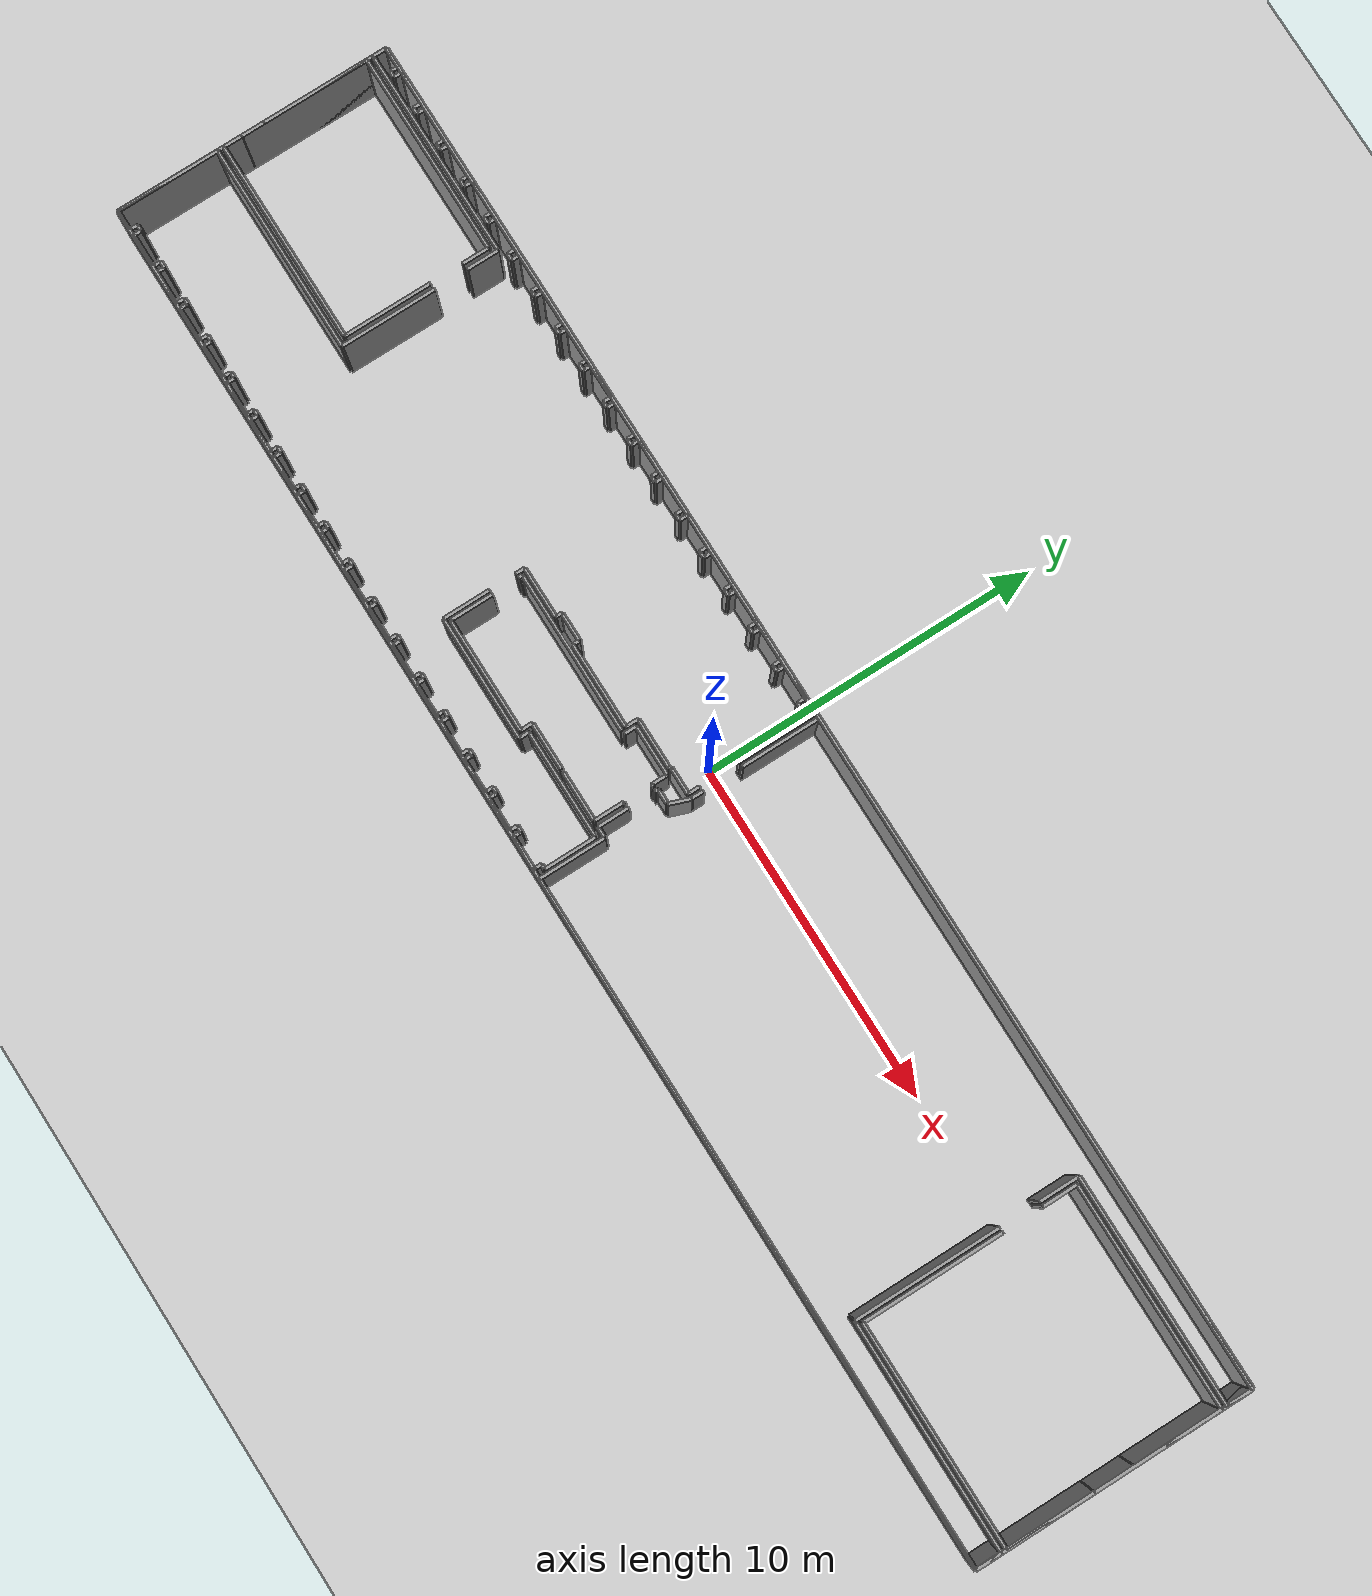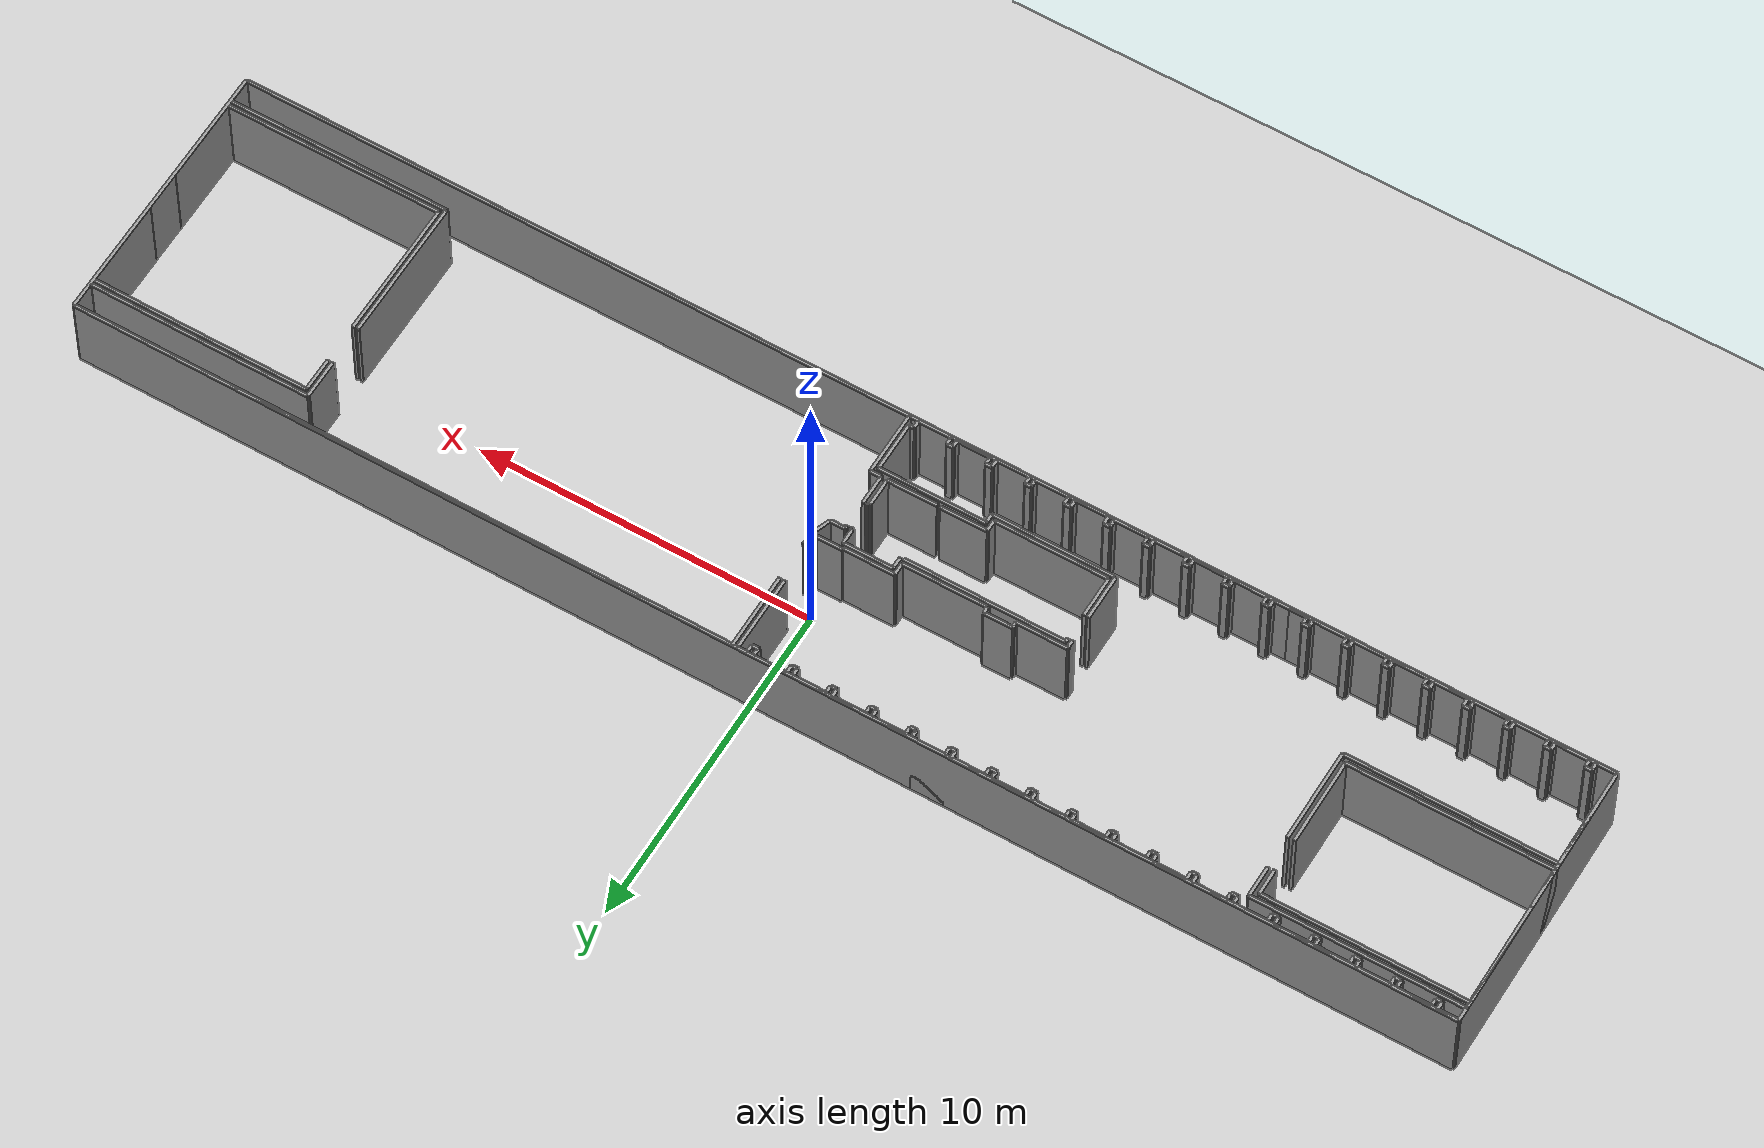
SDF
<sdf version="1.6">
  <world name="default">
    <light name="sun" type="directional">
      <cast_shadows>1</cast_shadows>
      <pose frame="">0 0 10 0 -0 0</pose>
      <diffuse>0.8 0.8 0.8 1</diffuse>
      <specular>0.1 0.1 0.1 1</specular>
      <attenuation>
        <range>1000</range>
        <constant>0.9</constant>
        <linear>0.01</linear>
        <quadratic>0.001</quadratic>
      </attenuation>
      <direction>-0.5 0.5 -1</direction>
    </light>
    <model name="ground_plane">
      <static>1</static>
      <link name="link">
        <collision name="collision">
          <geometry>
            <plane>
              <normal>0 0 1</normal>
              <size>100 100</size>
            </plane>
          </geometry>
          <surface>
            <friction>
              <ode>
                <mu>100</mu>
                <mu2>50</mu2>
              </ode>
              <torsional>
                <ode />
              </torsional>
            </friction>
            <contact>
              <ode />
            </contact>
            <bounce />
          </surface>
          <max_contacts>10</max_contacts>
        </collision>
        <visual name="visual">
          <cast_shadows>0</cast_shadows>
          <geometry>
            <plane>
              <normal>0 0 1</normal>
              <size>100 100</size>
            </plane>
          </geometry>
          <material>
            <script>
              <uri>file://media/materials/scripts/gazebo.material</uri>
              <name>Gazebo/Grey</name>
            </script>
          </material>
        </visual>
        <self_collide>0</self_collide>
        <kinematic>0</kinematic>
        <gravity>1</gravity>
      </link>
    </model>
    <gravity>0 0 -9.8</gravity>
    <magnetic_field>6e-06 2.3e-05 -4.2e-05</magnetic_field>
    <atmosphere type="adiabatic" />
    <physics default="0" name="default_physics" type="ode">
      <max_step_size>0.001</max_step_size>
      <real_time_factor>1</real_time_factor>
      <real_time_update_rate>1000</real_time_update_rate>
    </physics>
    <scene>
      <ambient>0.4 0.4 0.4 1</ambient>
      <background>0.7 0.7 0.7 1</background>
      <shadows>1</shadows>
    </scene>
    <spherical_coordinates>
      <surface_model>EARTH_WGS84</surface_model>
      <latitude_deg>0</latitude_deg>
      <longitude_deg>0</longitude_deg>
      <elevation>0</elevation>
      <heading_deg>0</heading_deg>
    </spherical_coordinates>
  <model name="0510025536_Layout1_PLAN5">
		<static>1</static>
		<link name="Wall_0">
			<collision name="Wall_0_Collision">
				<geometry>
					<box>
						<size>0.544916191178 0.1 2.5</size>
					</box>
				</geometry>
				<pose frame="">0.272458095589 0 1.25 0 0 0</pose>
			</collision>
			<visual name="Wall_0_Visual">
				<pose frame="">0.272458095589 0 1.25 0 0 0</pose>
				<geometry>
					<box>
						<size>0.544916191178 0.1 2.5</size>
					</box>
				</geometry>
				<material>
					<script>
						<uri>file://media/materials/scripts/gazebo.material</uri>
						<name>Gazebo/Grey</name>
					</script>
					<ambient>1 1 1 1</ambient>
				</material>
			</visual>
			<pose frame="">0.0 -4.97008552439 0 0 0 1.57079632679</pose>
		</link>
		<link name="Wall_1">
			<collision name="Wall_1_Collision">
				<geometry>
					<box>
						<size>3.15525282434 0.1 2.5</size>
					</box>
				</geometry>
				<pose frame="">1.57762641217 0 1.25 0 0 0</pose>
			</collision>
			<visual name="Wall_1_Visual">
				<pose frame="">1.57762641217 0 1.25 0 0 0</pose>
				<geometry>
					<box>
						<size>3.15525282434 0.1 2.5</size>
					</box>
				</geometry>
				<material>
					<script>
						<uri>file://media/materials/scripts/gazebo.material</uri>
						<name>Gazebo/Grey</name>
					</script>
					<ambient>1 1 1 1</ambient>
				</material>
			</visual>
			<pose frame="">0.0 -3.74491364959 0 0 0 1.57079632679</pose>
		</link>
		<link name="Wall_2">
			<collision name="Wall_2_Collision">
				<geometry>
					<box>
						<size>5.97464767254 0.1 2.5</size>
					</box>
				</geometry>
				<pose frame="">2.98732383627 0 1.25 0 0 0</pose>
			</collision>
			<visual name="Wall_2_Visual">
				<pose frame="">2.98732383627 0 1.25 0 0 0</pose>
				<geometry>
					<box>
						<size>5.97464767254 0.1 2.5</size>
					</box>
				</geometry>
				<material>
					<script>
						<uri>file://media/materials/scripts/gazebo.material</uri>
						<name>Gazebo/Grey</name>
					</script>
					<ambient>1 1 1 1</ambient>
				</material>
			</visual>
			<pose frame="">0.0 -0.589660825253 0 0 0 0.0</pose>
		</link>
		<link name="Wall_3">
			<collision name="Wall_3_Collision">
				<geometry>
					<box>
						<size>0.789003825088 0.1 2.5</size>
					</box>
				</geometry>
				<pose frame="">0.394501912544 0 1.25 0 0 0</pose>
			</collision>
			<visual name="Wall_3_Visual">
				<pose frame="">0.394501912544 0 1.25 0 0 0</pose>
				<geometry>
					<box>
						<size>0.789003825088 0.1 2.5</size>
					</box>
				</geometry>
				<material>
					<script>
						<uri>file://media/materials/scripts/gazebo.material</uri>
						<name>Gazebo/Grey</name>
					</script>
					<ambient>1 1 1 1</ambient>
				</material>
			</visual>
			<pose frame="">5.97464767254 -0.589660825253 0 0 0 -1.57079632679</pose>
		</link>
		<link name="Wall_4">
			<collision name="Wall_4_Collision">
				<geometry>
					<box>
						<size>2.6053169994 0.1 2.5</size>
					</box>
				</geometry>
				<pose frame="">1.3026584997 0 1.25 0 0 0</pose>
			</collision>
			<visual name="Wall_4_Visual">
				<pose frame="">1.3026584997 0 1.25 0 0 0</pose>
				<geometry>
					<box>
						<size>2.6053169994 0.1 2.5</size>
					</box>
				</geometry>
				<material>
					<script>
						<uri>file://media/materials/scripts/gazebo.material</uri>
						<name>Gazebo/Grey</name>
					</script>
					<ambient>1 1 1 1</ambient>
				</material>
			</visual>
			<pose frame="">5.97464767254 -2.35866871688 0 0 0 -1.57079632679</pose>
		</link>
		<link name="Wall_5">
			<collision name="Wall_5_Collision">
				<geometry>
					<box>
						<size>5.97465078634 0.1 2.5</size>
					</box>
				</geometry>
				<pose frame="">2.98732539317 0 1.25 0 0 0</pose>
			</collision>
			<visual name="Wall_5_Visual">
				<pose frame="">2.98732539317 0 1.25 0 0 0</pose>
				<geometry>
					<box>
						<size>5.97465078634 0.1 2.5</size>
					</box>
				</geometry>
				<material>
					<script>
						<uri>file://media/materials/scripts/gazebo.material</uri>
						<name>Gazebo/Grey</name>
					</script>
					<ambient>1 1 1 1</ambient>
				</material>
			</visual>
			<pose frame="">5.97464767254 -4.96398571628 0 0 0 -3.14057170536</pose>
		</link>
		<link name="Wall_6">
			<collision name="Wall_6_Collision">
				<geometry>
					<box>
						<size>4.75626183426 0.1 2.5</size>
					</box>
				</geometry>
				<pose frame="">2.37813091713 0 1.25 0 0 0</pose>
			</collision>
			<visual name="Wall_6_Visual">
				<pose frame="">2.37813091713 0 1.25 0 0 0</pose>
				<geometry>
					<box>
						<size>4.75626183426 0.1 2.5</size>
					</box>
				</geometry>
				<material>
					<script>
						<uri>file://media/materials/scripts/gazebo.material</uri>
						<name>Gazebo/Grey</name>
					</script>
					<ambient>1 1 1 1</ambient>
				</material>
			</visual>
			<pose frame="">13.7443417926 -4.4078230039 0 0 0 0.0</pose>
		</link>
		<link name="Wall_7">
			<collision name="Wall_7_Collision">
				<geometry>
					<box>
						<size>1.38529183769 0.1 2.5</size>
					</box>
				</geometry>
				<pose frame="">0.692645918847 0 1.25 0 0 0</pose>
			</collision>
			<visual name="Wall_7_Visual">
				<pose frame="">0.692645918847 0 1.25 0 0 0</pose>
				<geometry>
					<box>
						<size>1.38529183769 0.1 2.5</size>
					</box>
				</geometry>
				<material>
					<script>
						<uri>file://media/materials/scripts/gazebo.material</uri>
						<name>Gazebo/Grey</name>
					</script>
					<ambient>1 1 1 1</ambient>
				</material>
			</visual>
			<pose frame="">18.5006036268 -6.22759909011 0 0 0 3.14159265359</pose>
		</link>
		<link name="Wall_8">
			<collision name="Wall_8_Collision">
				<geometry>
					<box>
						<size>0.352708696039 0.1 2.5</size>
					</box>
				</geometry>
				<pose frame="">0.176354348019 0 1.25 0 0 0</pose>
			</collision>
			<visual name="Wall_8_Visual">
				<pose frame="">0.176354348019 0 1.25 0 0 0</pose>
				<geometry>
					<box>
						<size>0.352708696039 0.1 2.5</size>
					</box>
				</geometry>
				<material>
					<script>
						<uri>file://media/materials/scripts/gazebo.material</uri>
						<name>Gazebo/Grey</name>
					</script>
					<ambient>1 1 1 1</ambient>
				</material>
			</visual>
			<pose frame="">17.1153117891 -6.22759909011 0 0 0 -1.57079632679</pose>
		</link>
		<link name="Wall_9">
			<collision name="Wall_9_Collision">
				<geometry>
					<box>
						<size>3.36258276042 0.1 2.5</size>
					</box>
				</geometry>
				<pose frame="">1.68129138021 0 1.25 0 0 0</pose>
			</collision>
			<visual name="Wall_9_Visual">
				<pose frame="">1.68129138021 0 1.25 0 0 0</pose>
				<geometry>
					<box>
						<size>3.36258276042 0.1 2.5</size>
					</box>
				</geometry>
				<material>
					<script>
						<uri>file://media/materials/scripts/gazebo.material</uri>
						<name>Gazebo/Grey</name>
					</script>
					<ambient>1 1 1 1</ambient>
				</material>
			</visual>
			<pose frame="">17.1153117891 -6.58030778615 0 0 0 3.14159265359</pose>
		</link>
		<link name="Wall_10">
			<collision name="Wall_10_Collision">
				<geometry>
					<box>
						<size>1.26138948546 0.1 2.5</size>
					</box>
				</geometry>
				<pose frame="">0.630694742728 0 1.25 0 0 0</pose>
			</collision>
			<visual name="Wall_10_Visual">
				<pose frame="">0.630694742728 0 1.25 0 0 0</pose>
				<geometry>
					<box>
						<size>1.26138948546 0.1 2.5</size>
					</box>
				</geometry>
				<material>
					<script>
						<uri>file://media/materials/scripts/gazebo.material</uri>
						<name>Gazebo/Grey</name>
					</script>
					<ambient>1 1 1 1</ambient>
				</material>
			</visual>
			<pose frame="">13.7527290287 -6.58030778615 0 0 0 1.57079632679</pose>
		</link>
		<link name="Wall_11">
			<collision name="Wall_11_Collision">
				<geometry>
					<box>
						<size>0.122347523683 0.1 2.5</size>
					</box>
				</geometry>
				<pose frame="">0.0611737618414 0 1.25 0 0 0</pose>
			</collision>
			<visual name="Wall_11_Visual">
				<pose frame="">0.0611737618414 0 1.25 0 0 0</pose>
				<geometry>
					<box>
						<size>0.122347523683 0.1 2.5</size>
					</box>
				</geometry>
				<material>
					<script>
						<uri>file://media/materials/scripts/gazebo.material</uri>
						<name>Gazebo/Grey</name>
					</script>
					<ambient>1 1 1 1</ambient>
				</material>
			</visual>
			<pose frame="">13.7527290287 -4.52988270577 0 0 0 1.63940269551</pose>
		</link>
		<link name="Wall_12">
			<collision name="Wall_12_Collision">
				<geometry>
					<box>
						<size>0.512638039928 0.1 2.5</size>
					</box>
				</geometry>
				<pose frame="">0.256319019964 0 1.25 0 0 0</pose>
			</collision>
			<visual name="Wall_12_Visual">
				<pose frame="">0.256319019964 0 1.25 0 0 0</pose>
				<geometry>
					<box>
						<size>0.512638039928 0.1 2.5</size>
					</box>
				</geometry>
				<material>
					<script>
						<uri>file://media/materials/scripts/gazebo.material</uri>
						<name>Gazebo/Grey</name>
					</script>
					<ambient>1 1 1 1</ambient>
				</material>
			</visual>
			<pose frame="">9.40146903712 -8.18080847873 0 0 0 3.14159265359</pose>
		</link>
		<link name="Wall_13">
			<collision name="Wall_13_Collision">
				<geometry>
					<box>
						<size>0.235922786596 0.1 2.5</size>
					</box>
				</geometry>
				<pose frame="">0.117961393298 0 1.25 0 0 0</pose>
			</collision>
			<visual name="Wall_13_Visual">
				<pose frame="">0.117961393298 0 1.25 0 0 0</pose>
				<geometry>
					<box>
						<size>0.235922786596 0.1 2.5</size>
					</box>
				</geometry>
				<material>
					<script>
						<uri>file://media/materials/scripts/gazebo.material</uri>
						<name>Gazebo/Grey</name>
					</script>
					<ambient>1 1 1 1</ambient>
				</material>
			</visual>
			<pose frame="">8.88883099719 -8.18080847873 0 0 0 1.57079632679</pose>
		</link>
		<link name="Wall_14">
			<collision name="Wall_14_Collision">
				<geometry>
					<box>
						<size>0.182930703638 0.1 2.5</size>
					</box>
				</geometry>
				<pose frame="">0.0914653518191 0 1.25 0 0 0</pose>
			</collision>
			<visual name="Wall_14_Visual">
				<pose frame="">0.0914653518191 0 1.25 0 0 0</pose>
				<geometry>
					<box>
						<size>0.182930703638 0.1 2.5</size>
					</box>
				</geometry>
				<material>
					<script>
						<uri>file://media/materials/scripts/gazebo.material</uri>
						<name>Gazebo/Grey</name>
					</script>
					<ambient>1 1 1 1</ambient>
				</material>
			</visual>
			<pose frame="">8.88883099719 -7.94488569214 0 0 0 3.14159265359</pose>
		</link>
		<link name="Wall_15">
			<collision name="Wall_15_Collision">
				<geometry>
					<box>
						<size>0.229187581807 0.1 2.5</size>
					</box>
				</geometry>
				<pose frame="">0.114593790904 0 1.25 0 0 0</pose>
			</collision>
			<visual name="Wall_15_Visual">
				<pose frame="">0.114593790904 0 1.25 0 0 0</pose>
				<geometry>
					<box>
						<size>0.229187581807 0.1 2.5</size>
					</box>
				</geometry>
				<material>
					<script>
						<uri>file://media/materials/scripts/gazebo.material</uri>
						<name>Gazebo/Grey</name>
					</script>
					<ambient>1 1 1 1</ambient>
				</material>
			</visual>
			<pose frame="">8.70590029355 -7.94488569214 0 0 0 -1.57079632679</pose>
		</link>
		<link name="Wall_16">
			<collision name="Wall_16_Collision">
				<geometry>
					<box>
						<size>0.9815607884 0.1 2.5</size>
					</box>
				</geometry>
				<pose frame="">0.4907803942 0 1.25 0 0 0</pose>
			</collision>
			<visual name="Wall_16_Visual">
				<pose frame="">0.4907803942 0 1.25 0 0 0</pose>
				<geometry>
					<box>
						<size>0.9815607884 0.1 2.5</size>
					</box>
				</geometry>
				<material>
					<script>
						<uri>file://media/materials/scripts/gazebo.material</uri>
						<name>Gazebo/Grey</name>
					</script>
					<ambient>1 1 1 1</ambient>
				</material>
			</visual>
			<pose frame="">8.70590029355 -8.17407327394 0 0 0 3.14159265359</pose>
		</link>
		<link name="Wall_17">
			<collision name="Wall_17_Collision">
				<geometry>
					<box>
						<size>0.230903152838 0.1 2.5</size>
					</box>
				</geometry>
				<pose frame="">0.115451576419 0 1.25 0 0 0</pose>
			</collision>
			<visual name="Wall_17_Visual">
				<pose frame="">0.115451576419 0 1.25 0 0 0</pose>
				<geometry>
					<box>
						<size>0.230903152838 0.1 2.5</size>
					</box>
				</geometry>
				<material>
					<script>
						<uri>file://media/materials/scripts/gazebo.material</uri>
						<name>Gazebo/Grey</name>
					</script>
					<ambient>1 1 1 1</ambient>
				</material>
			</visual>
			<pose frame="">7.72433950515 -8.17407327394 0 0 0 1.57079632679</pose>
		</link>
		<link name="Wall_18">
			<collision name="Wall_18_Collision">
				<geometry>
					<box>
						<size>0.178864164898 0.1 2.5</size>
					</box>
				</geometry>
				<pose frame="">0.0894320824491 0 1.25 0 0 0</pose>
			</collision>
			<visual name="Wall_18_Visual">
				<pose frame="">0.0894320824491 0 1.25 0 0 0</pose>
				<geometry>
					<box>
						<size>0.178864164898 0.1 2.5</size>
					</box>
				</geometry>
				<material>
					<script>
						<uri>file://media/materials/scripts/gazebo.material</uri>
						<name>Gazebo/Grey</name>
					</script>
					<ambient>1 1 1 1</ambient>
				</material>
			</visual>
			<pose frame="">7.72433950515 -7.94317012111 0 0 0 3.14159265359</pose>
		</link>
		<link name="Wall_19">
			<collision name="Wall_19_Collision">
				<geometry>
					<box>
						<size>0.228043867787 0.1 2.5</size>
					</box>
				</geometry>
				<pose frame="">0.114021933893 0 1.25 0 0 0</pose>
			</collision>
			<visual name="Wall_19_Visual">
				<pose frame="">0.114021933893 0 1.25 0 0 0</pose>
				<geometry>
					<box>
						<size>0.228043867787 0.1 2.5</size>
					</box>
				</geometry>
				<material>
					<script>
						<uri>file://media/materials/scripts/gazebo.material</uri>
						<name>Gazebo/Grey</name>
					</script>
					<ambient>1 1 1 1</ambient>
				</material>
			</visual>
			<pose frame="">7.54547534025 -7.94317012111 0 0 0 -1.57079632679</pose>
		</link>
		<link name="Wall_20">
			<collision name="Wall_20_Collision">
				<geometry>
					<box>
						<size>0.975143281951 0.1 2.5</size>
					</box>
				</geometry>
				<pose frame="">0.487571640975 0 1.25 0 0 0</pose>
			</collision>
			<visual name="Wall_20_Visual">
				<pose frame="">0.487571640975 0 1.25 0 0 0</pose>
				<geometry>
					<box>
						<size>0.975143281951 0.1 2.5</size>
					</box>
				</geometry>
				<material>
					<script>
						<uri>file://media/materials/scripts/gazebo.material</uri>
						<name>Gazebo/Grey</name>
					</script>
					<ambient>1 1 1 1</ambient>
				</material>
			</visual>
			<pose frame="">7.54547534025 -8.17121398889 0 0 0 3.14159265359</pose>
		</link>
		<link name="Wall_21">
			<collision name="Wall_21_Collision">
				<geometry>
					<box>
						<size>0.226709534763 0.1 2.5</size>
					</box>
				</geometry>
				<pose frame="">0.113354767381 0 1.25 0 0 0</pose>
			</collision>
			<visual name="Wall_21_Visual">
				<pose frame="">0.113354767381 0 1.25 0 0 0</pose>
				<geometry>
					<box>
						<size>0.226709534763 0.1 2.5</size>
					</box>
				</geometry>
				<material>
					<script>
						<uri>file://media/materials/scripts/gazebo.material</uri>
						<name>Gazebo/Grey</name>
					</script>
					<ambient>1 1 1 1</ambient>
				</material>
			</visual>
			<pose frame="">6.5703320583 -8.17121398889 0 0 0 1.57079632679</pose>
		</link>
		<link name="Wall_22">
			<collision name="Wall_22_Collision">
				<geometry>
					<box>
						<size>0.183057782974 0.1 2.5</size>
					</box>
				</geometry>
				<pose frame="">0.091528891487 0 1.25 0 0 0</pose>
			</collision>
			<visual name="Wall_22_Visual">
				<pose frame="">0.091528891487 0 1.25 0 0 0</pose>
				<geometry>
					<box>
						<size>0.183057782974 0.1 2.5</size>
					</box>
				</geometry>
				<material>
					<script>
						<uri>file://media/materials/scripts/gazebo.material</uri>
						<name>Gazebo/Grey</name>
					</script>
					<ambient>1 1 1 1</ambient>
				</material>
			</visual>
			<pose frame="">6.5703320583 -7.94450445413 0 0 0 3.14159265359</pose>
		</link>
		<link name="Wall_23">
			<collision name="Wall_23_Collision">
				<geometry>
					<box>
						<size>0.233571818887 0.1 2.5</size>
					</box>
				</geometry>
				<pose frame="">0.116785909443 0 1.25 0 0 0</pose>
			</collision>
			<visual name="Wall_23_Visual">
				<pose frame="">0.116785909443 0 1.25 0 0 0</pose>
				<geometry>
					<box>
						<size>0.233571818887 0.1 2.5</size>
					</box>
				</geometry>
				<material>
					<script>
						<uri>file://media/materials/scripts/gazebo.material</uri>
						<name>Gazebo/Grey</name>
					</script>
					<ambient>1 1 1 1</ambient>
				</material>
			</visual>
			<pose frame="">6.38727427533 -7.94450445413 0 0 0 -1.57079632679</pose>
		</link>
		<link name="Wall_24">
			<collision name="Wall_24_Collision">
				<geometry>
					<box>
						<size>0.979654598366 0.1 2.5</size>
					</box>
				</geometry>
				<pose frame="">0.489827299183 0 1.25 0 0 0</pose>
			</collision>
			<visual name="Wall_24_Visual">
				<pose frame="">0.489827299183 0 1.25 0 0 0</pose>
				<geometry>
					<box>
						<size>0.979654598366 0.1 2.5</size>
					</box>
				</geometry>
				<material>
					<script>
						<uri>file://media/materials/scripts/gazebo.material</uri>
						<name>Gazebo/Grey</name>
					</script>
					<ambient>1 1 1 1</ambient>
				</material>
			</visual>
			<pose frame="">6.38727427533 -8.17807627302 0 0 0 3.14159265359</pose>
		</link>
		<link name="Wall_25">
			<collision name="Wall_25_Collision">
				<geometry>
					<box>
						<size>0.236748802277 0.1 2.5</size>
					</box>
				</geometry>
				<pose frame="">0.118374401139 0 1.25 0 0 0</pose>
			</collision>
			<visual name="Wall_25_Visual">
				<pose frame="">0.118374401139 0 1.25 0 0 0</pose>
				<geometry>
					<box>
						<size>0.236748802277 0.1 2.5</size>
					</box>
				</geometry>
				<material>
					<script>
						<uri>file://media/materials/scripts/gazebo.material</uri>
						<name>Gazebo/Grey</name>
					</script>
					<ambient>1 1 1 1</ambient>
				</material>
			</visual>
			<pose frame="">5.40761967696 -8.17807627302 0 0 0 1.57079632679</pose>
		</link>
		<link name="Wall_26">
			<collision name="Wall_26_Collision">
				<geometry>
					<box>
						<size>0.186107687029 0.1 2.5</size>
					</box>
				</geometry>
				<pose frame="">0.0930538435145 0 1.25 0 0 0</pose>
			</collision>
			<visual name="Wall_26_Visual">
				<pose frame="">0.0930538435145 0 1.25 0 0 0</pose>
				<geometry>
					<box>
						<size>0.186107687029 0.1 2.5</size>
					</box>
				</geometry>
				<material>
					<script>
						<uri>file://media/materials/scripts/gazebo.material</uri>
						<name>Gazebo/Grey</name>
					</script>
					<ambient>1 1 1 1</ambient>
				</material>
			</visual>
			<pose frame="">5.40761967696 -7.94132747074 0 0 0 3.14159265359</pose>
		</link>
		<link name="Wall_27">
			<collision name="Wall_27_Collision">
				<geometry>
					<box>
						<size>0.230394835496 0.1 2.5</size>
					</box>
				</geometry>
				<pose frame="">0.115197417748 0 1.25 0 0 0</pose>
			</collision>
			<visual name="Wall_27_Visual">
				<pose frame="">0.115197417748 0 1.25 0 0 0</pose>
				<geometry>
					<box>
						<size>0.230394835496 0.1 2.5</size>
					</box>
				</geometry>
				<material>
					<script>
						<uri>file://media/materials/scripts/gazebo.material</uri>
						<name>Gazebo/Grey</name>
					</script>
					<ambient>1 1 1 1</ambient>
				</material>
			</visual>
			<pose frame="">5.22151198994 -7.94132747074 0 0 0 -1.57079632679</pose>
		</link>
		<link name="Wall_28">
			<collision name="Wall_28_Collision">
				<geometry>
					<box>
						<size>0.965612331779 0.1 2.5</size>
					</box>
				</geometry>
				<pose frame="">0.482806165889 0 1.25 0 0 0</pose>
			</collision>
			<visual name="Wall_28_Visual">
				<pose frame="">0.482806165889 0 1.25 0 0 0</pose>
				<geometry>
					<box>
						<size>0.965612331779 0.1 2.5</size>
					</box>
				</geometry>
				<material>
					<script>
						<uri>file://media/materials/scripts/gazebo.material</uri>
						<name>Gazebo/Grey</name>
					</script>
					<ambient>1 1 1 1</ambient>
				</material>
			</visual>
			<pose frame="">5.22151198994 -8.17172230624 0 0 0 3.14159265359</pose>
		</link>
		<link name="Wall_29">
			<collision name="Wall_29_Collision">
				<geometry>
					<box>
						<size>0.232491644534 0.1 2.5</size>
					</box>
				</geometry>
				<pose frame="">0.116245822267 0 1.25 0 0 0</pose>
			</collision>
			<visual name="Wall_29_Visual">
				<pose frame="">0.116245822267 0 1.25 0 0 0</pose>
				<geometry>
					<box>
						<size>0.232491644534 0.1 2.5</size>
					</box>
				</geometry>
				<material>
					<script>
						<uri>file://media/materials/scripts/gazebo.material</uri>
						<name>Gazebo/Grey</name>
					</script>
					<ambient>1 1 1 1</ambient>
				</material>
			</visual>
			<pose frame="">4.25589965816 -8.17172230624 0 0 0 1.57079632679</pose>
		</link>
		<link name="Wall_30">
			<collision name="Wall_30_Collision">
				<geometry>
					<box>
						<size>0.191000241451 0.1 2.5</size>
					</box>
				</geometry>
				<pose frame="">0.0955001207254 0 1.25 0 0 0</pose>
			</collision>
			<visual name="Wall_30_Visual">
				<pose frame="">0.0955001207254 0 1.25 0 0 0</pose>
				<geometry>
					<box>
						<size>0.191000241451 0.1 2.5</size>
					</box>
				</geometry>
				<material>
					<script>
						<uri>file://media/materials/scripts/gazebo.material</uri>
						<name>Gazebo/Grey</name>
					</script>
					<ambient>1 1 1 1</ambient>
				</material>
			</visual>
			<pose frame="">4.25589965816 -7.9392306617 0 0 0 3.14159265359</pose>
		</link>
		<link name="Wall_31">
			<collision name="Wall_31_Collision">
				<geometry>
					<box>
						<size>0.238527912976 0.1 2.5</size>
					</box>
				</geometry>
				<pose frame="">0.119263956488 0 1.25 0 0 0</pose>
			</collision>
			<visual name="Wall_31_Visual">
				<pose frame="">0.119263956488 0 1.25 0 0 0</pose>
				<geometry>
					<box>
						<size>0.238527912976 0.1 2.5</size>
					</box>
				</geometry>
				<material>
					<script>
						<uri>file://media/materials/scripts/gazebo.material</uri>
						<name>Gazebo/Grey</name>
					</script>
					<ambient>1 1 1 1</ambient>
				</material>
			</visual>
			<pose frame="">4.06489941671 -7.9392306617 0 0 0 -1.57079632679</pose>
		</link>
		<link name="Wall_32">
			<collision name="Wall_32_Collision">
				<geometry>
					<box>
						<size>0.978714211282 0.1 2.5</size>
					</box>
				</geometry>
				<pose frame="">0.489357105641 0 1.25 0 0 0</pose>
			</collision>
			<visual name="Wall_32_Visual">
				<pose frame="">0.489357105641 0 1.25 0 0 0</pose>
				<geometry>
					<box>
						<size>0.978714211282 0.1 2.5</size>
					</box>
				</geometry>
				<material>
					<script>
						<uri>file://media/materials/scripts/gazebo.material</uri>
						<name>Gazebo/Grey</name>
					</script>
					<ambient>1 1 1 1</ambient>
				</material>
			</visual>
			<pose frame="">4.06489941671 -8.17775857468 0 0 0 3.14159265359</pose>
		</link>
		<link name="Wall_33">
			<collision name="Wall_33_Collision">
				<geometry>
					<box>
						<size>0.240052865004 0.1 2.5</size>
					</box>
				</geometry>
				<pose frame="">0.120026432502 0 1.25 0 0 0</pose>
			</collision>
			<visual name="Wall_33_Visual">
				<pose frame="">0.120026432502 0 1.25 0 0 0</pose>
				<geometry>
					<box>
						<size>0.240052865004 0.1 2.5</size>
					</box>
				</geometry>
				<material>
					<script>
						<uri>file://media/materials/scripts/gazebo.material</uri>
						<name>Gazebo/Grey</name>
					</script>
					<ambient>1 1 1 1</ambient>
				</material>
			</visual>
			<pose frame="">3.08618520542 -8.17775857468 0 0 0 1.57079632679</pose>
		</link>
		<link name="Wall_34">
			<collision name="Wall_34_Collision">
				<geometry>
					<box>
						<size>0.171963756973 0.1 2.5</size>
					</box>
				</geometry>
				<pose frame="">0.0859818784867 0 1.25 0 0 0</pose>
			</collision>
			<visual name="Wall_34_Visual">
				<pose frame="">0.0859818784867 0 1.25 0 0 0</pose>
				<geometry>
					<box>
						<size>0.171963756973 0.1 2.5</size>
					</box>
				</geometry>
				<material>
					<script>
						<uri>file://media/materials/scripts/gazebo.material</uri>
						<name>Gazebo/Grey</name>
					</script>
					<ambient>1 1 1 1</ambient>
				</material>
			</visual>
			<pose frame="">3.08618520542 -7.93770570967 0 0 0 3.14159265359</pose>
		</link>
		<link name="Wall_35">
			<collision name="Wall_35_Collision">
				<geometry>
					<box>
						<size>0.234906151911 0.1 2.5</size>
					</box>
				</geometry>
				<pose frame="">0.117453075955 0 1.25 0 0 0</pose>
			</collision>
			<visual name="Wall_35_Visual">
				<pose frame="">0.117453075955 0 1.25 0 0 0</pose>
				<geometry>
					<box>
						<size>0.234906151911 0.1 2.5</size>
					</box>
				</geometry>
				<material>
					<script>
						<uri>file://media/materials/scripts/gazebo.material</uri>
						<name>Gazebo/Grey</name>
					</script>
					<ambient>1 1 1 1</ambient>
				</material>
			</visual>
			<pose frame="">2.91422144845 -7.93770570967 0 0 0 -1.57079632679</pose>
		</link>
		<link name="Wall_36">
			<collision name="Wall_36_Collision">
				<geometry>
					<box>
						<size>0.977665806763 0.1 2.5</size>
					</box>
				</geometry>
				<pose frame="">0.488832903382 0 1.25 0 0 0</pose>
			</collision>
			<visual name="Wall_36_Visual">
				<pose frame="">0.488832903382 0 1.25 0 0 0</pose>
				<geometry>
					<box>
						<size>0.977665806763 0.1 2.5</size>
					</box>
				</geometry>
				<material>
					<script>
						<uri>file://media/materials/scripts/gazebo.material</uri>
						<name>Gazebo/Grey</name>
					</script>
					<ambient>1 1 1 1</ambient>
				</material>
			</visual>
			<pose frame="">2.91422144845 -8.17261186159 0 0 0 3.14159265359</pose>
		</link>
		<link name="Wall_37">
			<collision name="Wall_37_Collision">
				<geometry>
					<box>
						<size>0.229378200811 0.1 2.5</size>
					</box>
				</geometry>
				<pose frame="">0.114689100405 0 1.25 0 0 0</pose>
			</collision>
			<visual name="Wall_37_Visual">
				<pose frame="">0.114689100405 0 1.25 0 0 0</pose>
				<geometry>
					<box>
						<size>0.229378200811 0.1 2.5</size>
					</box>
				</geometry>
				<material>
					<script>
						<uri>file://media/materials/scripts/gazebo.material</uri>
						<name>Gazebo/Grey</name>
					</script>
					<ambient>1 1 1 1</ambient>
				</material>
			</visual>
			<pose frame="">1.93655564169 -8.17261186159 0 0 0 1.57079632679</pose>
		</link>
		<link name="Wall_38">
			<collision name="Wall_38_Collision">
				<geometry>
					<box>
						<size>0.186901932877 0.1 2.5</size>
					</box>
				</geometry>
				<pose frame="">0.0934509664383 0 1.25 0 0 0</pose>
			</collision>
			<visual name="Wall_38_Visual">
				<pose frame="">0.0934509664383 0 1.25 0 0 0</pose>
				<geometry>
					<box>
						<size>0.186901932877 0.1 2.5</size>
					</box>
				</geometry>
				<material>
					<script>
						<uri>file://media/materials/scripts/gazebo.material</uri>
						<name>Gazebo/Grey</name>
					</script>
					<ambient>1 1 1 1</ambient>
				</material>
			</visual>
			<pose frame="">1.93655564169 -7.94323366077 0 0 0 3.14159265359</pose>
		</link>
		<link name="Wall_39">
			<collision name="Wall_39_Collision">
				<geometry>
					<box>
						<size>0.229314661143 0.1 2.5</size>
					</box>
				</geometry>
				<pose frame="">0.114657330571 0 1.25 0 0 0</pose>
			</collision>
			<visual name="Wall_39_Visual">
				<pose frame="">0.114657330571 0 1.25 0 0 0</pose>
				<geometry>
					<box>
						<size>0.229314661143 0.1 2.5</size>
					</box>
				</geometry>
				<material>
					<script>
						<uri>file://media/materials/scripts/gazebo.material</uri>
						<name>Gazebo/Grey</name>
					</script>
					<ambient>1 1 1 1</ambient>
				</material>
			</visual>
			<pose frame="">1.74965370881 -7.94323366077 0 0 0 -1.57079632679</pose>
		</link>
		<link name="Wall_40">
			<collision name="Wall_40_Collision">
				<geometry>
					<box>
						<size>0.976833437115 0.1 2.5</size>
					</box>
				</geometry>
				<pose frame="">0.488416718557 0 1.25 0 0 0</pose>
			</collision>
			<visual name="Wall_40_Visual">
				<pose frame="">0.488416718557 0 1.25 0 0 0</pose>
				<geometry>
					<box>
						<size>0.976833437115 0.1 2.5</size>
					</box>
				</geometry>
				<material>
					<script>
						<uri>file://media/materials/scripts/gazebo.material</uri>
						<name>Gazebo/Grey</name>
					</script>
					<ambient>1 1 1 1</ambient>
				</material>
			</visual>
			<pose frame="">1.74965370881 -8.17254832192 0 0 0 3.14159265359</pose>
		</link>
		<link name="Wall_41">
			<collision name="Wall_41_Collision">
				<geometry>
					<box>
						<size>0.227090772769 0.1 2.5</size>
					</box>
				</geometry>
				<pose frame="">0.113545386385 0 1.25 0 0 0</pose>
			</collision>
			<visual name="Wall_41_Visual">
				<pose frame="">0.113545386385 0 1.25 0 0 0</pose>
				<geometry>
					<box>
						<size>0.227090772769 0.1 2.5</size>
					</box>
				</geometry>
				<material>
					<script>
						<uri>file://media/materials/scripts/gazebo.material</uri>
						<name>Gazebo/Grey</name>
					</script>
					<ambient>1 1 1 1</ambient>
				</material>
			</visual>
			<pose frame="">0.772820271696 -8.17254832192 0 0 0 1.57079632679</pose>
		</link>
		<link name="Wall_42">
			<collision name="Wall_42_Collision">
				<geometry>
					<box>
						<size>0.180624213697 0.1 2.5</size>
					</box>
				</geometry>
				<pose frame="">0.0903121068483 0 1.25 0 0 0</pose>
			</collision>
			<visual name="Wall_42_Visual">
				<pose frame="">0.0903121068483 0 1.25 0 0 0</pose>
				<geometry>
					<box>
						<size>0.180624213697 0.1 2.5</size>
					</box>
				</geometry>
				<material>
					<script>
						<uri>file://media/materials/scripts/gazebo.material</uri>
						<name>Gazebo/Grey</name>
					</script>
					<ambient>1 1 1 1</ambient>
				</material>
			</visual>
			<pose frame="">0.772820271696 -7.94545754915 0 0 0 3.14159265359</pose>
		</link>
		<link name="Wall_43">
			<collision name="Wall_43_Collision">
				<geometry>
					<box>
						<size>0.23840083364 0.1 2.5</size>
					</box>
				</geometry>
				<pose frame="">0.11920041682 0 1.25 0 0 0</pose>
			</collision>
			<visual name="Wall_43_Visual">
				<pose frame="">0.11920041682 0 1.25 0 0 0</pose>
				<geometry>
					<box>
						<size>0.23840083364 0.1 2.5</size>
					</box>
				</geometry>
				<material>
					<script>
						<uri>file://media/materials/scripts/gazebo.material</uri>
						<name>Gazebo/Grey</name>
					</script>
					<ambient>1 1 1 1</ambient>
				</material>
			</visual>
			<pose frame="">0.592196057999 -7.94545754915 0 0 0 -1.57079632679</pose>
		</link>
		<link name="Wall_44">
			<collision name="Wall_44_Collision">
				<geometry>
					<box>
						<size>0.587011221105 0.1 2.5</size>
					</box>
				</geometry>
				<pose frame="">0.293505610553 0 1.25 0 0 0</pose>
			</collision>
			<visual name="Wall_44_Visual">
				<pose frame="">0.293505610553 0 1.25 0 0 0</pose>
				<geometry>
					<box>
						<size>0.587011221105 0.1 2.5</size>
					</box>
				</geometry>
				<material>
					<script>
						<uri>file://media/materials/scripts/gazebo.material</uri>
						<name>Gazebo/Grey</name>
					</script>
					<ambient>1 1 1 1</ambient>
				</material>
			</visual>
			<pose frame="">0.592196057999 -8.18385838279 0 0 0 3.14159265359</pose>
		</link>
		<link name="Wall_45">
			<collision name="Wall_45_Collision">
				<geometry>
					<box>
						<size>3.02772871103 0.1 2.5</size>
					</box>
				</geometry>
				<pose frame="">1.51386435552 0 1.25 0 0 0</pose>
			</collision>
			<visual name="Wall_45_Visual">
				<pose frame="">1.51386435552 0 1.25 0 0 0</pose>
				<geometry>
					<box>
						<size>3.02772871103 0.1 2.5</size>
					</box>
				</geometry>
				<material>
					<script>
						<uri>file://media/materials/scripts/gazebo.material</uri>
						<name>Gazebo/Grey</name>
					</script>
					<ambient>1 1 1 1</ambient>
				</material>
			</visual>
			<pose frame="">0.00518483689367 -8.18385838279 0 0 0 1.57079632679</pose>
		</link>
		<link name="Wall_46">
			<collision name="Wall_46_Collision">
				<geometry>
					<box>
						<size>6.15874750607 0.1 2.5</size>
					</box>
				</geometry>
				<pose frame="">3.07937375303 0 1.25 0 0 0</pose>
			</collision>
			<visual name="Wall_46_Visual">
				<pose frame="">3.07937375303 0 1.25 0 0 0</pose>
				<geometry>
					<box>
						<size>6.15874750607 0.1 2.5</size>
					</box>
				</geometry>
				<material>
					<script>
						<uri>file://media/materials/scripts/gazebo.material</uri>
						<name>Gazebo/Grey</name>
					</script>
					<ambient>1 1 1 1</ambient>
				</material>
			</visual>
			<pose frame="">0.00518483689367 -5.15612967175 0 0 0 0.0</pose>
		</link>
		<link name="Wall_47">
			<collision name="Wall_47_Collision">
				<geometry>
					<box>
						<size>2.81823842625 0.1 2.5</size>
					</box>
				</geometry>
				<pose frame="">1.40911921312 0 1.25 0 0 0</pose>
			</collision>
			<visual name="Wall_47_Visual">
				<pose frame="">1.40911921312 0 1.25 0 0 0</pose>
				<geometry>
					<box>
						<size>2.81823842625 0.1 2.5</size>
					</box>
				</geometry>
				<material>
					<script>
						<uri>file://media/materials/scripts/gazebo.material</uri>
						<name>Gazebo/Grey</name>
					</script>
					<ambient>1 1 1 1</ambient>
				</material>
			</visual>
			<pose frame="">6.16393234296 -5.15612967175 0 0 0 1.57079632679</pose>
		</link>
		<link name="Wall_48">
			<collision name="Wall_48_Collision">
				<geometry>
					<box>
						<size>0.954194253472 0.1 2.5</size>
					</box>
				</geometry>
				<pose frame="">0.477097126736 0 1.25 0 0 0</pose>
			</collision>
			<visual name="Wall_48_Visual">
				<pose frame="">0.477097126736 0 1.25 0 0 0</pose>
				<geometry>
					<box>
						<size>0.954194253472 0.1 2.5</size>
					</box>
				</geometry>
				<material>
					<script>
						<uri>file://media/materials/scripts/gazebo.material</uri>
						<name>Gazebo/Grey</name>
					</script>
					<ambient>1 1 1 1</ambient>
				</material>
			</visual>
			<pose frame="">6.16393234296 -1.36065115452 0 0 0 1.57079632679</pose>
		</link>
		<link name="Wall_49">
			<collision name="Wall_49_Collision">
				<geometry>
					<box>
						<size>6.16335413198 0.1 2.5</size>
					</box>
				</geometry>
				<pose frame="">3.08167706599 0 1.25 0 0 0</pose>
			</collision>
			<visual name="Wall_49_Visual">
				<pose frame="">3.08167706599 0 1.25 0 0 0</pose>
				<geometry>
					<box>
						<size>6.16335413198 0.1 2.5</size>
					</box>
				</geometry>
				<material>
					<script>
						<uri>file://media/materials/scripts/gazebo.material</uri>
						<name>Gazebo/Grey</name>
					</script>
					<ambient>1 1 1 1</ambient>
				</material>
			</visual>
			<pose frame="">6.16393234296 -0.406456901043 0 0 0 3.14159265359</pose>
		</link>
		<link name="Wall_50">
			<collision name="Wall_50_Collision">
				<geometry>
					<box>
						<size>0.405707132963 0.1 2.5</size>
					</box>
				</geometry>
				<pose frame="">0.202853566482 0 1.25 0 0 0</pose>
			</collision>
			<visual name="Wall_50_Visual">
				<pose frame="">0.202853566482 0 1.25 0 0 0</pose>
				<geometry>
					<box>
						<size>0.405707132963 0.1 2.5</size>
					</box>
				</geometry>
				<material>
					<script>
						<uri>file://media/materials/scripts/gazebo.material</uri>
						<name>Gazebo/Grey</name>
					</script>
					<ambient>1 1 1 1</ambient>
				</material>
			</visual>
			<pose frame="">0.000578210977113 -0.406456901043 0 0 0 1.57079632679</pose>
		</link>
		<link name="Wall_51">
			<collision name="Wall_51_Collision">
				<geometry>
					<box>
						<size>0.595779695264 0.1 2.5</size>
					</box>
				</geometry>
				<pose frame="">0.297889847632 0 1.25 0 0 0</pose>
			</collision>
			<visual name="Wall_51_Visual">
				<pose frame="">0.297889847632 0 1.25 0 0 0</pose>
				<geometry>
					<box>
						<size>0.595779695264 0.1 2.5</size>
					</box>
				</geometry>
				<material>
					<script>
						<uri>file://media/materials/scripts/gazebo.material</uri>
						<name>Gazebo/Grey</name>
					</script>
					<ambient>1 1 1 1</ambient>
				</material>
			</visual>
			<pose frame="">0.000578210977113 -0.000749768080212 0 0 0 0.0</pose>
		</link>
		<link name="Wall_52">
			<collision name="Wall_52_Collision">
				<geometry>
					<box>
						<size>0.24448157985 0.1 2.5</size>
					</box>
				</geometry>
				<pose frame="">0.122240789925 0 1.25 0 0 0</pose>
			</collision>
			<visual name="Wall_52_Visual">
				<pose frame="">0.122240789925 0 1.25 0 0 0</pose>
				<geometry>
					<box>
						<size>0.24448157985 0.1 2.5</size>
					</box>
				</geometry>
				<material>
					<script>
						<uri>file://media/materials/scripts/gazebo.material</uri>
						<name>Gazebo/Grey</name>
					</script>
					<ambient>1 1 1 1</ambient>
				</material>
			</visual>
			<pose frame="">0.596357906241 -0.000749768080212 0 0 0 -1.57079632679</pose>
		</link>
		<link name="Wall_53">
			<collision name="Wall_53_Collision">
				<geometry>
					<box>
						<size>0.175807906876 0.1 2.5</size>
					</box>
				</geometry>
				<pose frame="">0.0879039534381 0 1.25 0 0 0</pose>
			</collision>
			<visual name="Wall_53_Visual">
				<pose frame="">0.0879039534381 0 1.25 0 0 0</pose>
				<geometry>
					<box>
						<size>0.175807906876 0.1 2.5</size>
					</box>
				</geometry>
				<material>
					<script>
						<uri>file://media/materials/scripts/gazebo.material</uri>
						<name>Gazebo/Grey</name>
					</script>
					<ambient>1 1 1 1</ambient>
				</material>
			</visual>
			<pose frame="">0.596357906241 -0.245231347931 0 0 0 0.0</pose>
		</link>
		<link name="Wall_54">
			<collision name="Wall_54_Collision">
				<geometry>
					<box>
						<size>0.241736666201 0.1 2.5</size>
					</box>
				</geometry>
				<pose frame="">0.1208683331 0 1.25 0 0 0</pose>
			</collision>
			<visual name="Wall_54_Visual">
				<pose frame="">0.1208683331 0 1.25 0 0 0</pose>
				<geometry>
					<box>
						<size>0.241736666201 0.1 2.5</size>
					</box>
				</geometry>
				<material>
					<script>
						<uri>file://media/materials/scripts/gazebo.material</uri>
						<name>Gazebo/Grey</name>
					</script>
					<ambient>1 1 1 1</ambient>
				</material>
			</visual>
			<pose frame="">0.772165813117 -0.245231347931 0 0 0 1.57079632679</pose>
		</link>
		<link name="Wall_55">
			<collision name="Wall_55_Collision">
				<geometry>
					<box>
						<size>0.977456125859 0.1 2.5</size>
					</box>
				</geometry>
				<pose frame="">0.48872806293 0 1.25 0 0 0</pose>
			</collision>
			<visual name="Wall_55_Visual">
				<pose frame="">0.48872806293 0 1.25 0 0 0</pose>
				<geometry>
					<box>
						<size>0.977456125859 0.1 2.5</size>
					</box>
				</geometry>
				<material>
					<script>
						<uri>file://media/materials/scripts/gazebo.material</uri>
						<name>Gazebo/Grey</name>
					</script>
					<ambient>1 1 1 1</ambient>
				</material>
			</visual>
			<pose frame="">0.772165813117 -0.0034946817298 0 0 0 0.0</pose>
		</link>
		<link name="Wall_56">
			<collision name="Wall_56_Collision">
				<geometry>
					<box>
						<size>0.254876669505 0.1 2.5</size>
					</box>
				</geometry>
				<pose frame="">0.127438334752 0 1.25 0 0 0</pose>
			</collision>
			<visual name="Wall_56_Visual">
				<pose frame="">0.127438334752 0 1.25 0 0 0</pose>
				<geometry>
					<box>
						<size>0.254876669505 0.1 2.5</size>
					</box>
				</geometry>
				<material>
					<script>
						<uri>file://media/materials/scripts/gazebo.material</uri>
						<name>Gazebo/Grey</name>
					</script>
					<ambient>1 1 1 1</ambient>
				</material>
			</visual>
			<pose frame="">1.74962193898 -0.0034946817298 0 0 0 -1.57079632679</pose>
		</link>
		<link name="Wall_57">
			<collision name="Wall_57_Collision">
				<geometry>
					<box>
						<size>0.181539184913 0.1 2.5</size>
					</box>
				</geometry>
				<pose frame="">0.0907695924566 0 1.25 0 0 0</pose>
			</collision>
			<visual name="Wall_57_Visual">
				<pose frame="">0.0907695924566 0 1.25 0 0 0</pose>
				<geometry>
					<box>
						<size>0.181539184913 0.1 2.5</size>
					</box>
				</geometry>
				<material>
					<script>
						<uri>file://media/materials/scripts/gazebo.material</uri>
						<name>Gazebo/Grey</name>
					</script>
					<ambient>1 1 1 1</ambient>
				</material>
			</visual>
			<pose frame="">1.74962193898 -0.258371351235 0 0 0 0.0</pose>
		</link>
		<link name="Wall_58">
			<collision name="Wall_58_Collision">
				<geometry>
					<box>
						<size>0.248427393222 0.1 2.5</size>
					</box>
				</geometry>
				<pose frame="">0.124213696611 0 1.25 0 0 0</pose>
			</collision>
			<visual name="Wall_58_Visual">
				<pose frame="">0.124213696611 0 1.25 0 0 0</pose>
				<geometry>
					<box>
						<size>0.248427393222 0.1 2.5</size>
					</box>
				</geometry>
				<material>
					<script>
						<uri>file://media/materials/scripts/gazebo.material</uri>
						<name>Gazebo/Grey</name>
					</script>
					<ambient>1 1 1 1</ambient>
				</material>
			</visual>
			<pose frame="">1.93116112389 -0.258371351235 0 0 0 1.57079632679</pose>
		</link>
		<link name="Wall_59">
			<collision name="Wall_59_Collision">
				<geometry>
					<box>
						<size>0.976579278444 0.1 2.5</size>
					</box>
				</geometry>
				<pose frame="">0.488289639222 0 1.25 0 0 0</pose>
			</collision>
			<visual name="Wall_59_Visual">
				<pose frame="">0.488289639222 0 1.25 0 0 0</pose>
				<geometry>
					<box>
						<size>0.976579278444 0.1 2.5</size>
					</box>
				</geometry>
				<material>
					<script>
						<uri>file://media/materials/scripts/gazebo.material</uri>
						<name>Gazebo/Grey</name>
					</script>
					<ambient>1 1 1 1</ambient>
				</material>
			</visual>
			<pose frame="">1.93116112389 -0.00994395801299 0 0 0 0.0</pose>
		</link>
		<link name="Wall_60">
			<collision name="Wall_60_Collision">
				<geometry>
					<box>
						<size>0.244163881511 0.1 2.5</size>
					</box>
				</geometry>
				<pose frame="">0.122081940756 0 1.25 0 0 0</pose>
			</collision>
			<visual name="Wall_60_Visual">
				<pose frame="">0.122081940756 0 1.25 0 0 0</pose>
				<geometry>
					<box>
						<size>0.244163881511 0.1 2.5</size>
					</box>
				</geometry>
				<material>
					<script>
						<uri>file://media/materials/scripts/gazebo.material</uri>
						<name>Gazebo/Grey</name>
					</script>
					<ambient>1 1 1 1</ambient>
				</material>
			</visual>
			<pose frame="">2.90774040233 -0.00994395801299 0 0 0 -1.57079632679</pose>
		</link>
		<link name="Wall_61">
			<collision name="Wall_61_Collision">
				<geometry>
					<box>
						<size>0.179442375875 0.1 2.5</size>
					</box>
				</geometry>
				<pose frame="">0.0897211879376 0 1.25 0 0 0</pose>
			</collision>
			<visual name="Wall_61_Visual">
				<pose frame="">0.0897211879376 0 1.25 0 0 0</pose>
				<geometry>
					<box>
						<size>0.179442375875 0.1 2.5</size>
					</box>
				</geometry>
				<material>
					<script>
						<uri>file://media/materials/scripts/gazebo.material</uri>
						<name>Gazebo/Grey</name>
					</script>
					<ambient>1 1 1 1</ambient>
				</material>
			</visual>
			<pose frame="">2.90774040233 -0.254107839524 0 0 0 0.0</pose>
		</link>
		<link name="Wall_62">
			<collision name="Wall_62_Collision">
				<geometry>
					<box>
						<size>0.247175661766 0.1 2.5</size>
					</box>
				</geometry>
				<pose frame="">0.123587830883 0 1.25 0 0 0</pose>
			</collision>
			<visual name="Wall_62_Visual">
				<pose frame="">0.123587830883 0 1.25 0 0 0</pose>
				<geometry>
					<box>
						<size>0.247175661766 0.1 2.5</size>
					</box>
				</geometry>
				<material>
					<script>
						<uri>file://media/materials/scripts/gazebo.material</uri>
						<name>Gazebo/Grey</name>
					</script>
					<ambient>1 1 1 1</ambient>
				</material>
			</visual>
			<pose frame="">3.08718277821 -0.254107839524 0 0 0 1.57079632679</pose>
		</link>
		<link name="Wall_63">
			<collision name="Wall_63_Collision">
				<geometry>
					<box>
						<size>0.979495749196 0.1 2.5</size>
					</box>
				</geometry>
				<pose frame="">0.489747874598 0 1.25 0 0 0</pose>
			</collision>
			<visual name="Wall_63_Visual">
				<pose frame="">0.489747874598 0 1.25 0 0 0</pose>
				<geometry>
					<box>
						<size>0.979495749196 0.1 2.5</size>
					</box>
				</geometry>
				<material>
					<script>
						<uri>file://media/materials/scripts/gazebo.material</uri>
						<name>Gazebo/Grey</name>
					</script>
					<ambient>1 1 1 1</ambient>
				</material>
			</visual>
			<pose frame="">3.08718277821 -0.00693217775857 0 0 0 0.0</pose>
		</link>
		<link name="Wall_64">
			<collision name="Wall_64_Collision">
				<geometry>
					<box>
						<size>0.249285178737 0.1 2.5</size>
					</box>
				</geometry>
				<pose frame="">0.124642589369 0 1.25 0 0 0</pose>
			</collision>
			<visual name="Wall_64_Visual">
				<pose frame="">0.124642589369 0 1.25 0 0 0</pose>
				<geometry>
					<box>
						<size>0.249285178737 0.1 2.5</size>
					</box>
				</geometry>
				<material>
					<script>
						<uri>file://media/materials/scripts/gazebo.material</uri>
						<name>Gazebo/Grey</name>
					</script>
					<ambient>1 1 1 1</ambient>
				</material>
			</visual>
			<pose frame="">4.0666785274 -0.00693217775857 0 0 0 -1.57079632679</pose>
		</link>
		<link name="Wall_65">
			<collision name="Wall_65_Collision">
				<geometry>
					<box>
						<size>0.18318486231 0.1 2.5</size>
					</box>
				</geometry>
				<pose frame="">0.0915924311548 0 1.25 0 0 0</pose>
			</collision>
			<visual name="Wall_65_Visual">
				<pose frame="">0.0915924311548 0 1.25 0 0 0</pose>
				<geometry>
					<box>
						<size>0.18318486231 0.1 2.5</size>
					</box>
				</geometry>
				<material>
					<script>
						<uri>file://media/materials/scripts/gazebo.material</uri>
						<name>Gazebo/Grey</name>
					</script>
					<ambient>1 1 1 1</ambient>
				</material>
			</visual>
			<pose frame="">4.0666785274 -0.256217356496 0 0 0 0.0</pose>
		</link>
		<link name="Wall_66">
			<collision name="Wall_66_Collision">
				<geometry>
					<box>
						<size>0.255467588415 0.1 2.5</size>
					</box>
				</geometry>
				<pose frame="">0.127733794208 0 1.25 0 0 0</pose>
			</collision>
			<visual name="Wall_66_Visual">
				<pose frame="">0.127733794208 0 1.25 0 0 0</pose>
				<geometry>
					<box>
						<size>0.255467588415 0.1 2.5</size>
					</box>
				</geometry>
				<material>
					<script>
						<uri>file://media/materials/scripts/gazebo.material</uri>
						<name>Gazebo/Grey</name>
					</script>
					<ambient>1 1 1 1</ambient>
				</material>
			</visual>
			<pose frame="">4.24986338971 -0.256217356496 0 0 0 1.57079632679</pose>
		</link>
		<link name="Wall_67">
			<collision name="Wall_67_Collision">
				<geometry>
					<box>
						<size>0.972411076235 0.1 2.5</size>
					</box>
				</geometry>
				<pose frame="">0.486205538117 0 1.25 0 0 0</pose>
			</collision>
			<visual name="Wall_67_Visual">
				<pose frame="">0.486205538117 0 1.25 0 0 0</pose>
				<geometry>
					<box>
						<size>0.972411076235 0.1 2.5</size>
					</box>
				</geometry>
				<material>
					<script>
						<uri>file://media/materials/scripts/gazebo.material</uri>
						<name>Gazebo/Grey</name>
					</script>
					<ambient>1 1 1 1</ambient>
				</material>
			</visual>
			<pose frame="">4.24986338971 -0.000749768080212 0 0 0 0.0</pose>
		</link>
		<link name="Wall_68">
			<collision name="Wall_68_Collision">
				<geometry>
					<box>
						<size>0.248484578923 0.1 2.5</size>
					</box>
				</geometry>
				<pose frame="">0.124242289461 0 1.25 0 0 0</pose>
			</collision>
			<visual name="Wall_68_Visual">
				<pose frame="">0.124242289461 0 1.25 0 0 0</pose>
				<geometry>
					<box>
						<size>0.248484578923 0.1 2.5</size>
					</box>
				</geometry>
				<material>
					<script>
						<uri>file://media/materials/scripts/gazebo.material</uri>
						<name>Gazebo/Grey</name>
					</script>
					<ambient>1 1 1 1</ambient>
				</material>
			</visual>
			<pose frame="">5.22227446595 -0.000749768080212 0 0 0 -1.57079632679</pose>
		</link>
		<link name="Wall_69">
			<collision name="Wall_69_Collision">
				<geometry>
					<box>
						<size>0.188839892745 0.1 2.5</size>
					</box>
				</geometry>
				<pose frame="">0.0944199463725 0 1.25 0 0 0</pose>
			</collision>
			<visual name="Wall_69_Visual">
				<pose frame="">0.0944199463725 0 1.25 0 0 0</pose>
				<geometry>
					<box>
						<size>0.188839892745 0.1 2.5</size>
					</box>
				</geometry>
				<material>
					<script>
						<uri>file://media/materials/scripts/gazebo.material</uri>
						<name>Gazebo/Grey</name>
					</script>
					<ambient>1 1 1 1</ambient>
				</material>
			</visual>
			<pose frame="">5.22227446595 -0.249234347003 0 0 0 0.0</pose>
		</link>
		<link name="Wall_70">
			<collision name="Wall_70_Collision">
				<geometry>
					<box>
						<size>0.240224422107 0.1 2.5</size>
					</box>
				</geometry>
				<pose frame="">0.120112211053 0 1.25 0 0 0</pose>
			</collision>
			<visual name="Wall_70_Visual">
				<pose frame="">0.120112211053 0 1.25 0 0 0</pose>
				<geometry>
					<box>
						<size>0.240224422107 0.1 2.5</size>
					</box>
				</geometry>
				<material>
					<script>
						<uri>file://media/materials/scripts/gazebo.material</uri>
						<name>Gazebo/Grey</name>
					</script>
					<ambient>1 1 1 1</ambient>
				</material>
			</visual>
			<pose frame="">5.41111435869 -0.249234347003 0 0 0 1.57079632679</pose>
		</link>
		<link name="Wall_71">
			<collision name="Wall_71_Collision">
				<geometry>
					<box>
						<size>0.968153918491 0.1 2.5</size>
					</box>
				</geometry>
				<pose frame="">0.484076959246 0 1.25 0 0 0</pose>
			</collision>
			<visual name="Wall_71_Visual">
				<pose frame="">0.484076959246 0 1.25 0 0 0</pose>
				<geometry>
					<box>
						<size>0.968153918491 0.1 2.5</size>
					</box>
				</geometry>
				<material>
					<script>
						<uri>file://media/materials/scripts/gazebo.material</uri>
						<name>Gazebo/Grey</name>
					</script>
					<ambient>1 1 1 1</ambient>
				</material>
			</visual>
			<pose frame="">5.41111435869 -0.00900992489611 0 0 0 0.0</pose>
		</link>
		<link name="Wall_72">
			<collision name="Wall_72_Collision">
				<geometry>
					<box>
						<size>0.241399905961 0.1 2.5</size>
					</box>
				</geometry>
				<pose frame="">0.120699952981 0 1.25 0 0 0</pose>
			</collision>
			<visual name="Wall_72_Visual">
				<pose frame="">0.120699952981 0 1.25 0 0 0</pose>
				<geometry>
					<box>
						<size>0.241399905961 0.1 2.5</size>
					</box>
				</geometry>
				<material>
					<script>
						<uri>file://media/materials/scripts/gazebo.material</uri>
						<name>Gazebo/Grey</name>
					</script>
					<ambient>1 1 1 1</ambient>
				</material>
			</visual>
			<pose frame="">6.37926827719 -0.00900992489611 0 0 0 -1.57079632679</pose>
		</link>
		<link name="Wall_73">
			<collision name="Wall_73_Collision">
				<geometry>
					<box>
						<size>0.194876161187 0.1 2.5</size>
					</box>
				</geometry>
				<pose frame="">0.0974380805937 0 1.25 0 0 0</pose>
			</collision>
			<visual name="Wall_73_Visual">
				<pose frame="">0.0974380805937 0 1.25 0 0 0</pose>
				<geometry>
					<box>
						<size>0.194876161187 0.1 2.5</size>
					</box>
				</geometry>
				<material>
					<script>
						<uri>file://media/materials/scripts/gazebo.material</uri>
						<name>Gazebo/Grey</name>
					</script>
					<ambient>1 1 1 1</ambient>
				</material>
			</visual>
			<pose frame="">6.37926827719 -0.250409830857 0 0 0 0.0</pose>
		</link>
		<link name="Wall_74">
			<collision name="Wall_74_Collision">
				<geometry>
					<box>
						<size>0.24335692773 0.1 2.5</size>
					</box>
				</geometry>
				<pose frame="">0.121678463865 0 1.25 0 0 0</pose>
			</collision>
			<visual name="Wall_74_Visual">
				<pose frame="">0.121678463865 0 1.25 0 0 0</pose>
				<geometry>
					<box>
						<size>0.24335692773 0.1 2.5</size>
					</box>
				</geometry>
				<material>
					<script>
						<uri>file://media/materials/scripts/gazebo.material</uri>
						<name>Gazebo/Grey</name>
					</script>
					<ambient>1 1 1 1</ambient>
				</material>
			</visual>
			<pose frame="">6.57414443837 -0.250409830857 0 0 0 1.57079632679</pose>
		</link>
		<link name="Wall_75">
			<collision name="Wall_75_Collision">
				<geometry>
					<box>
						<size>0.970123648194 0.1 2.5</size>
					</box>
				</geometry>
				<pose frame="">0.485061824097 0 1.25 0 0 0</pose>
			</collision>
			<visual name="Wall_75_Visual">
				<pose frame="">0.485061824097 0 1.25 0 0 0</pose>
				<geometry>
					<box>
						<size>0.970123648194 0.1 2.5</size>
					</box>
				</geometry>
				<material>
					<script>
						<uri>file://media/materials/scripts/gazebo.material</uri>
						<name>Gazebo/Grey</name>
					</script>
					<ambient>1 1 1 1</ambient>
				</material>
			</visual>
			<pose frame="">6.57414443837 -0.00705290312742 0 0 0 0.0</pose>
		</link>
		<link name="Wall_76">
			<collision name="Wall_76_Collision">
				<geometry>
					<box>
						<size>0.249132683534 0.1 2.5</size>
					</box>
				</geometry>
				<pose frame="">0.124566341767 0 1.25 0 0 0</pose>
			</collision>
			<visual name="Wall_76_Visual">
				<pose frame="">0.124566341767 0 1.25 0 0 0</pose>
				<geometry>
					<box>
						<size>0.249132683534 0.1 2.5</size>
					</box>
				</geometry>
				<material>
					<script>
						<uri>file://media/materials/scripts/gazebo.material</uri>
						<name>Gazebo/Grey</name>
					</script>
					<ambient>1 1 1 1</ambient>
				</material>
			</visual>
			<pose frame="">7.54426808657 -0.00705290312742 0 0 0 -1.57079632679</pose>
		</link>
		<link name="Wall_77">
			<collision name="Wall_77_Collision">
				<geometry>
					<box>
						<size>0.176957974864 0.1 2.5</size>
					</box>
				</geometry>
				<pose frame="">0.0884789874319 0 1.25 0 0 0</pose>
			</collision>
			<visual name="Wall_77_Visual">
				<pose frame="">0.0884789874319 0 1.25 0 0 0</pose>
				<geometry>
					<box>
						<size>0.176957974864 0.1 2.5</size>
					</box>
				</geometry>
				<material>
					<script>
						<uri>file://media/materials/scripts/gazebo.material</uri>
						<name>Gazebo/Grey</name>
					</script>
					<ambient>1 1 1 1</ambient>
				</material>
			</visual>
			<pose frame="">7.54426808657 -0.256185586662 0 0 0 0.0</pose>
		</link>
		<link name="Wall_78">
			<collision name="Wall_78_Collision">
				<geometry>
					<box>
						<size>0.247175661766 0.1 2.5</size>
					</box>
				</geometry>
				<pose frame="">0.123587830883 0 1.25 0 0 0</pose>
			</collision>
			<visual name="Wall_78_Visual">
				<pose frame="">0.123587830883 0 1.25 0 0 0</pose>
				<geometry>
					<box>
						<size>0.247175661766 0.1 2.5</size>
					</box>
				</geometry>
				<material>
					<script>
						<uri>file://media/materials/scripts/gazebo.material</uri>
						<name>Gazebo/Grey</name>
					</script>
					<ambient>1 1 1 1</ambient>
				</material>
			</visual>
			<pose frame="">7.72122606143 -0.256185586662 0 0 0 1.57079632679</pose>
		</link>
		<link name="Wall_79">
			<collision name="Wall_79_Collision">
				<geometry>
					<box>
						<size>0.980798312386 0.1 2.5</size>
					</box>
				</geometry>
				<pose frame="">0.490399156193 0 1.25 0 0 0</pose>
			</collision>
			<visual name="Wall_79_Visual">
				<pose frame="">0.490399156193 0 1.25 0 0 0</pose>
				<geometry>
					<box>
						<size>0.980798312386 0.1 2.5</size>
					</box>
				</geometry>
				<material>
					<script>
						<uri>file://media/materials/scripts/gazebo.material</uri>
						<name>Gazebo/Grey</name>
					</script>
					<ambient>1 1 1 1</ambient>
				</material>
			</visual>
			<pose frame="">7.72122606143 -0.00900992489611 0 0 0 0.0</pose>
		</link>
		<link name="Wall_80">
			<collision name="Wall_80_Collision">
				<geometry>
					<box>
						<size>0.243833475239 0.1 2.5</size>
					</box>
				</geometry>
				<pose frame="">0.121916737619 0 1.25 0 0 0</pose>
			</collision>
			<visual name="Wall_80_Visual">
				<pose frame="">0.121916737619 0 1.25 0 0 0</pose>
				<geometry>
					<box>
						<size>0.243833475239 0.1 2.5</size>
					</box>
				</geometry>
				<material>
					<script>
						<uri>file://media/materials/scripts/gazebo.material</uri>
						<name>Gazebo/Grey</name>
					</script>
					<ambient>1 1 1 1</ambient>
				</material>
			</visual>
			<pose frame="">8.70202437382 -0.00900992489611 0 0 0 -1.57079632679</pose>
		</link>
		<link name="Wall_81">
			<collision name="Wall_81_Collision">
				<geometry>
					<box>
						<size>0.17880062523 0.1 2.5</size>
					</box>
				</geometry>
				<pose frame="">0.0894003126152 0 1.25 0 0 0</pose>
			</collision>
			<visual name="Wall_81_Visual">
				<pose frame="">0.0894003126152 0 1.25 0 0 0</pose>
				<geometry>
					<box>
						<size>0.17880062523 0.1 2.5</size>
					</box>
				</geometry>
				<material>
					<script>
						<uri>file://media/materials/scripts/gazebo.material</uri>
						<name>Gazebo/Grey</name>
					</script>
					<ambient>1 1 1 1</ambient>
				</material>
			</visual>
			<pose frame="">8.70202437382 -0.252843400135 0 0 0 0.0</pose>
		</link>
		<link name="Wall_82">
			<collision name="Wall_82_Collision">
				<geometry>
					<box>
						<size>0.242028948673 0.1 2.5</size>
					</box>
				</geometry>
				<pose frame="">0.121014474336 0 1.25 0 0 0</pose>
			</collision>
			<visual name="Wall_82_Visual">
				<pose frame="">0.121014474336 0 1.25 0 0 0</pose>
				<geometry>
					<box>
						<size>0.242028948673 0.1 2.5</size>
					</box>
				</geometry>
				<material>
					<script>
						<uri>file://media/materials/scripts/gazebo.material</uri>
						<name>Gazebo/Grey</name>
					</script>
					<ambient>1 1 1 1</ambient>
				</material>
			</visual>
			<pose frame="">8.88082499905 -0.252843400135 0 0 0 1.57079632679</pose>
		</link>
		<link name="Wall_83">
			<collision name="Wall_83_Collision">
				<geometry>
					<box>
						<size>0.97895566202 0.1 2.5</size>
					</box>
				</geometry>
				<pose frame="">0.48947783101 0 1.25 0 0 0</pose>
			</collision>
			<visual name="Wall_83_Visual">
				<pose frame="">0.48947783101 0 1.25 0 0 0</pose>
				<geometry>
					<box>
						<size>0.97895566202 0.1 2.5</size>
					</box>
				</geometry>
				<material>
					<script>
						<uri>file://media/materials/scripts/gazebo.material</uri>
						<name>Gazebo/Grey</name>
					</script>
					<ambient>1 1 1 1</ambient>
				</material>
			</visual>
			<pose frame="">8.88082499905 -0.010814451462 0 0 0 0.0</pose>
		</link>
		<link name="Wall_84">
			<collision name="Wall_84_Collision">
				<geometry>
					<box>
						<size>0.241221994891 0.1 2.5</size>
					</box>
				</geometry>
				<pose frame="">0.120610997446 0 1.25 0 0 0</pose>
			</collision>
			<visual name="Wall_84_Visual">
				<pose frame="">0.120610997446 0 1.25 0 0 0</pose>
				<geometry>
					<box>
						<size>0.241221994891 0.1 2.5</size>
					</box>
				</geometry>
				<material>
					<script>
						<uri>file://media/materials/scripts/gazebo.material</uri>
						<name>Gazebo/Grey</name>
					</script>
					<ambient>1 1 1 1</ambient>
				</material>
			</visual>
			<pose frame="">9.85978066107 -0.010814451462 0 0 0 -1.57079632679</pose>
		</link>
		<link name="Wall_85">
			<collision name="Wall_85_Collision">
				<geometry>
					<box>
						<size>0.183693179652 0.1 2.5</size>
					</box>
				</geometry>
				<pose frame="">0.091846589826 0 1.25 0 0 0</pose>
			</collision>
			<visual name="Wall_85_Visual">
				<pose frame="">0.091846589826 0 1.25 0 0 0</pose>
				<geometry>
					<box>
						<size>0.183693179652 0.1 2.5</size>
					</box>
				</geometry>
				<material>
					<script>
						<uri>file://media/materials/scripts/gazebo.material</uri>
						<name>Gazebo/Grey</name>
					</script>
					<ambient>1 1 1 1</ambient>
				</material>
			</visual>
			<pose frame="">9.85978066107 -0.252036446353 0 0 0 0.0</pose>
		</link>
		<link name="Wall_86">
			<collision name="Wall_86_Collision">
				<geometry>
					<box>
						<size>0.245104268595 0.1 2.5</size>
					</box>
				</geometry>
				<pose frame="">0.122552134297 0 1.25 0 0 0</pose>
			</collision>
			<visual name="Wall_86_Visual">
				<pose frame="">0.122552134297 0 1.25 0 0 0</pose>
				<geometry>
					<box>
						<size>0.245104268595 0.1 2.5</size>
					</box>
				</geometry>
				<material>
					<script>
						<uri>file://media/materials/scripts/gazebo.material</uri>
						<name>Gazebo/Grey</name>
					</script>
					<ambient>1 1 1 1</ambient>
				</material>
			</visual>
			<pose frame="">10.0434738407 -0.252036446353 0 0 0 1.57079632679</pose>
		</link>
		<link name="Wall_87">
			<collision name="Wall_87_Collision">
				<geometry>
					<box>
						<size>0.976414075307 0.1 2.5</size>
					</box>
				</geometry>
				<pose frame="">0.488207037654 0 1.25 0 0 0</pose>
			</collision>
			<visual name="Wall_87_Visual">
				<pose frame="">0.488207037654 0 1.25 0 0 0</pose>
				<geometry>
					<box>
						<size>0.976414075307 0.1 2.5</size>
					</box>
				</geometry>
				<material>
					<script>
						<uri>file://media/materials/scripts/gazebo.material</uri>
						<name>Gazebo/Grey</name>
					</script>
					<ambient>1 1 1 1</ambient>
				</material>
			</visual>
			<pose frame="">10.0434738407 -0.00693217775857 0 0 0 0.0</pose>
		</link>
		<link name="Wall_88">
			<collision name="Wall_88_Collision">
				<geometry>
					<box>
						<size>0.237536694158 0.1 2.5</size>
					</box>
				</geometry>
				<pose frame="">0.118768347079 0 1.25 0 0 0</pose>
			</collision>
			<visual name="Wall_88_Visual">
				<pose frame="">0.118768347079 0 1.25 0 0 0</pose>
				<geometry>
					<box>
						<size>0.237536694158 0.1 2.5</size>
					</box>
				</geometry>
				<material>
					<script>
						<uri>file://media/materials/scripts/gazebo.material</uri>
						<name>Gazebo/Grey</name>
					</script>
					<ambient>1 1 1 1</ambient>
				</material>
			</visual>
			<pose frame="">11.019887916 -0.00693217775857 0 0 0 -1.57079632679</pose>
		</link>
		<link name="Wall_89">
			<collision name="Wall_89_Collision">
				<geometry>
					<box>
						<size>0.181659910282 0.1 2.5</size>
					</box>
				</geometry>
				<pose frame="">0.090829955141 0 1.25 0 0 0</pose>
			</collision>
			<visual name="Wall_89_Visual">
				<pose frame="">0.090829955141 0 1.25 0 0 0</pose>
				<geometry>
					<box>
						<size>0.181659910282 0.1 2.5</size>
					</box>
				</geometry>
				<material>
					<script>
						<uri>file://media/materials/scripts/gazebo.material</uri>
						<name>Gazebo/Grey</name>
					</script>
					<ambient>1 1 1 1</ambient>
				</material>
			</visual>
			<pose frame="">11.019887916 -0.244468871917 0 0 0 0.0</pose>
		</link>
		<link name="Wall_90">
			<collision name="Wall_90_Collision">
				<geometry>
					<box>
						<size>0.243102769059 0.1 2.5</size>
					</box>
				</geometry>
				<pose frame="">0.121551384529 0 1.25 0 0 0</pose>
			</collision>
			<visual name="Wall_90_Visual">
				<pose frame="">0.121551384529 0 1.25 0 0 0</pose>
				<geometry>
					<box>
						<size>0.243102769059 0.1 2.5</size>
					</box>
				</geometry>
				<material>
					<script>
						<uri>file://media/materials/scripts/gazebo.material</uri>
						<name>Gazebo/Grey</name>
					</script>
					<ambient>1 1 1 1</ambient>
				</material>
			</visual>
			<pose frame="">11.2015478263 -0.244468871917 0 0 0 1.57079632679</pose>
		</link>
		<link name="Wall_91">
			<collision name="Wall_91_Collision">
				<geometry>
					<box>
						<size>0.972411076235 0.1 2.5</size>
					</box>
				</geometry>
				<pose frame="">0.486205538117 0 1.25 0 0 0</pose>
			</collision>
			<visual name="Wall_91_Visual">
				<pose frame="">0.486205538117 0 1.25 0 0 0</pose>
				<geometry>
					<box>
						<size>0.972411076235 0.1 2.5</size>
					</box>
				</geometry>
				<material>
					<script>
						<uri>file://media/materials/scripts/gazebo.material</uri>
						<name>Gazebo/Grey</name>
					</script>
					<ambient>1 1 1 1</ambient>
				</material>
			</visual>
			<pose frame="">11.2015478263 -0.00136610285801 0 0 0 0.0</pose>
		</link>
		<link name="Wall_92">
			<collision name="Wall_92_Collision">
				<geometry>
					<box>
						<size>0.245834974775 0.1 2.5</size>
					</box>
				</geometry>
				<pose frame="">0.122917487387 0 1.25 0 0 0</pose>
			</collision>
			<visual name="Wall_92_Visual">
				<pose frame="">0.122917487387 0 1.25 0 0 0</pose>
				<geometry>
					<box>
						<size>0.245834974775 0.1 2.5</size>
					</box>
				</geometry>
				<material>
					<script>
						<uri>file://media/materials/scripts/gazebo.material</uri>
						<name>Gazebo/Grey</name>
					</script>
					<ambient>1 1 1 1</ambient>
				</material>
			</visual>
			<pose frame="">12.1739589025 -0.00136610285801 0 0 0 -1.57079632679</pose>
		</link>
		<link name="Wall_93">
			<collision name="Wall_93_Collision">
				<geometry>
					<box>
						<size>0.19392306617 0.1 2.5</size>
					</box>
				</geometry>
				<pose frame="">0.0969615330851 0 1.25 0 0 0</pose>
			</collision>
			<visual name="Wall_93_Visual">
				<pose frame="">0.0969615330851 0 1.25 0 0 0</pose>
				<geometry>
					<box>
						<size>0.19392306617 0.1 2.5</size>
					</box>
				</geometry>
				<material>
					<script>
						<uri>file://media/materials/scripts/gazebo.material</uri>
						<name>Gazebo/Grey</name>
					</script>
					<ambient>1 1 1 1</ambient>
				</material>
			</visual>
			<pose frame="">12.1739589025 -0.247201077633 0 0 0 0.0</pose>
		</link>
		<link name="Wall_94">
			<collision name="Wall_94_Collision">
				<geometry>
					<box>
						<size>0.241736666201 0.1 2.5</size>
					</box>
				</geometry>
				<pose frame="">0.1208683331 0 1.25 0 0 0</pose>
			</collision>
			<visual name="Wall_94_Visual">
				<pose frame="">0.1208683331 0 1.25 0 0 0</pose>
				<geometry>
					<box>
						<size>0.241736666201 0.1 2.5</size>
					</box>
				</geometry>
				<material>
					<script>
						<uri>file://media/materials/scripts/gazebo.material</uri>
						<name>Gazebo/Grey</name>
					</script>
					<ambient>1 1 1 1</ambient>
				</material>
			</visual>
			<pose frame="">12.3678819687 -0.247201077633 0 0 0 1.57079632679</pose>
		</link>
		<link name="Wall_95">
			<collision name="Wall_95_Collision">
				<geometry>
					<box>
						<size>0.962880126063 0.1 2.5</size>
					</box>
				</geometry>
				<pose frame="">0.481440063031 0 1.25 0 0 0</pose>
			</collision>
			<visual name="Wall_95_Visual">
				<pose frame="">0.481440063031 0 1.25 0 0 0</pose>
				<geometry>
					<box>
						<size>0.962880126063 0.1 2.5</size>
					</box>
				</geometry>
				<material>
					<script>
						<uri>file://media/materials/scripts/gazebo.material</uri>
						<name>Gazebo/Grey</name>
					</script>
					<ambient>1 1 1 1</ambient>
				</material>
			</visual>
			<pose frame="">12.3678819687 -0.00546441143206 0 0 0 0.0</pose>
		</link>
		<link name="Wall_96">
			<collision name="Wall_96_Collision">
				<geometry>
					<box>
						<size>0.243102769059 0.1 2.5</size>
					</box>
				</geometry>
				<pose frame="">0.121551384529 0 1.25 0 0 0</pose>
			</collision>
			<visual name="Wall_96_Visual">
				<pose frame="">0.121551384529 0 1.25 0 0 0</pose>
				<geometry>
					<box>
						<size>0.243102769059 0.1 2.5</size>
					</box>
				</geometry>
				<material>
					<script>
						<uri>file://media/materials/scripts/gazebo.material</uri>
						<name>Gazebo/Grey</name>
					</script>
					<ambient>1 1 1 1</ambient>
				</material>
			</visual>
			<pose frame="">13.3307620948 -0.00546441143206 0 0 0 -1.57079632679</pose>
		</link>
		<link name="Wall_97">
			<collision name="Wall_97_Collision">
				<geometry>
					<box>
						<size>0.189792987762 0.1 2.5</size>
					</box>
				</geometry>
				<pose frame="">0.0948964938811 0 1.25 0 0 0</pose>
			</collision>
			<visual name="Wall_97_Visual">
				<pose frame="">0.0948964938811 0 1.25 0 0 0</pose>
				<geometry>
					<box>
						<size>0.189792987762 0.1 2.5</size>
					</box>
				</geometry>
				<material>
					<script>
						<uri>file://media/materials/scripts/gazebo.material</uri>
						<name>Gazebo/Grey</name>
					</script>
					<ambient>1 1 1 1</ambient>
				</material>
			</visual>
			<pose frame="">13.3307620948 -0.248567180491 0 0 0 0.0</pose>
		</link>
		<link name="Wall_98">
			<collision name="Wall_98_Collision">
				<geometry>
					<box>
						<size>0.240370563343 0.1 2.5</size>
					</box>
				</geometry>
				<pose frame="">0.120185281671 0 1.25 0 0 0</pose>
			</collision>
			<visual name="Wall_98_Visual">
				<pose frame="">0.120185281671 0 1.25 0 0 0</pose>
				<geometry>
					<box>
						<size>0.240370563343 0.1 2.5</size>
					</box>
				</geometry>
				<material>
					<script>
						<uri>file://media/materials/scripts/gazebo.material</uri>
						<name>Gazebo/Grey</name>
					</script>
					<ambient>1 1 1 1</ambient>
				</material>
			</visual>
			<pose frame="">13.5205550825 -0.248567180491 0 0 0 1.57079632679</pose>
		</link>
		<link name="Wall_99">
			<collision name="Wall_99_Collision">
				<geometry>
					<box>
						<size>0.978320265342 0.1 2.5</size>
					</box>
				</geometry>
				<pose frame="">0.489160132671 0 1.25 0 0 0</pose>
			</collision>
			<visual name="Wall_99_Visual">
				<pose frame="">0.489160132671 0 1.25 0 0 0</pose>
				<geometry>
					<box>
						<size>0.978320265342 0.1 2.5</size>
					</box>
				</geometry>
				<material>
					<script>
						<uri>file://media/materials/scripts/gazebo.material</uri>
						<name>Gazebo/Grey</name>
					</script>
					<ambient>1 1 1 1</ambient>
				</material>
			</visual>
			<pose frame="">13.5205550825 -0.00819661714809 0 0 0 0.0</pose>
		</link>
		<link name="Wall_100">
			<collision name="Wall_100_Collision">
				<geometry>
					<box>
						<size>0.237638357627 0.1 2.5</size>
					</box>
				</geometry>
				<pose frame="">0.118819178813 0 1.25 0 0 0</pose>
			</collision>
			<visual name="Wall_100_Visual">
				<pose frame="">0.118819178813 0 1.25 0 0 0</pose>
				<geometry>
					<box>
						<size>0.237638357627 0.1 2.5</size>
					</box>
				</geometry>
				<material>
					<script>
						<uri>file://media/materials/scripts/gazebo.material</uri>
						<name>Gazebo/Grey</name>
					</script>
					<ambient>1 1 1 1</ambient>
				</material>
			</visual>
			<pose frame="">14.4988753479 -0.00819661714809 0 0 0 -1.57079632679</pose>
		</link>
		<link name="Wall_101">
			<collision name="Wall_101_Collision">
				<geometry>
					<box>
						<size>0.185281671347 0.1 2.5</size>
					</box>
				</geometry>
				<pose frame="">0.0926408356737 0 1.25 0 0 0</pose>
			</collision>
			<visual name="Wall_101_Visual">
				<pose frame="">0.0926408356737 0 1.25 0 0 0</pose>
				<geometry>
					<box>
						<size>0.185281671347 0.1 2.5</size>
					</box>
				</geometry>
				<material>
					<script>
						<uri>file://media/materials/scripts/gazebo.material</uri>
						<name>Gazebo/Grey</name>
					</script>
					<ambient>1 1 1 1</ambient>
				</material>
			</visual>
			<pose frame="">14.4988753479 -0.245834974775 0 0 0 0.0</pose>
		</link>
		<link name="Wall_102">
			<collision name="Wall_102_Collision">
				<geometry>
					<box>
						<size>0.245834974775 0.1 2.5</size>
					</box>
				</geometry>
				<pose frame="">0.122917487387 0 1.25 0 0 0</pose>
			</collision>
			<visual name="Wall_102_Visual">
				<pose frame="">0.122917487387 0 1.25 0 0 0</pose>
				<geometry>
					<box>
						<size>0.245834974775 0.1 2.5</size>
					</box>
				</geometry>
				<material>
					<script>
						<uri>file://media/materials/scripts/gazebo.material</uri>
						<name>Gazebo/Grey</name>
					</script>
					<ambient>1 1 1 1</ambient>
				</material>
			</visual>
			<pose frame="">14.6841570192 -0.245834974775 0 0 0 1.57079632679</pose>
		</link>
		<link name="Wall_103">
			<collision name="Wall_103_Collision">
				<geometry>
					<box>
						<size>0.965231093772 0.1 2.5</size>
					</box>
				</geometry>
				<pose frame="">0.482615546886 0 1.25 0 0 0</pose>
			</collision>
			<visual name="Wall_103_Visual">
				<pose frame="">0.482615546886 0 1.25 0 0 0</pose>
				<geometry>
					<box>
						<size>0.965231093772 0.1 2.5</size>
					</box>
				</geometry>
				<material>
					<script>
						<uri>file://media/materials/scripts/gazebo.material</uri>
						<name>Gazebo/Grey</name>
					</script>
					<ambient>1 1 1 1</ambient>
				</material>
			</visual>
			<pose frame="">14.6841570192 -0.0 0 0 0 0.0</pose>
		</link>
		<link name="Wall_104">
			<collision name="Wall_104_Collision">
				<geometry>
					<box>
						<size>0.253472442846 0.1 2.5</size>
					</box>
				</geometry>
				<pose frame="">0.126736221423 0 1.25 0 0 0</pose>
			</collision>
			<visual name="Wall_104_Visual">
				<pose frame="">0.126736221423 0 1.25 0 0 0</pose>
				<geometry>
					<box>
						<size>0.253472442846 0.1 2.5</size>
					</box>
				</geometry>
				<material>
					<script>
						<uri>file://media/materials/scripts/gazebo.material</uri>
						<name>Gazebo/Grey</name>
					</script>
					<ambient>1 1 1 1</ambient>
				</material>
			</visual>
			<pose frame="">15.649388113 -0.0 0 0 0 -1.57079632679</pose>
		</link>
		<link name="Wall_105">
			<collision name="Wall_105_Collision">
				<geometry>
					<box>
						<size>0.187314940717 0.1 2.5</size>
					</box>
				</geometry>
				<pose frame="">0.0936574703587 0 1.25 0 0 0</pose>
			</collision>
			<visual name="Wall_105_Visual">
				<pose frame="">0.0936574703587 0 1.25 0 0 0</pose>
				<geometry>
					<box>
						<size>0.187314940717 0.1 2.5</size>
					</box>
				</geometry>
				<material>
					<script>
						<uri>file://media/materials/scripts/gazebo.material</uri>
						<name>Gazebo/Grey</name>
					</script>
					<ambient>1 1 1 1</ambient>
				</material>
			</visual>
			<pose frame="">15.649388113 -0.253472442846 0 0 0 0.0</pose>
		</link>
		<link name="Wall_106">
			<collision name="Wall_106_Collision">
				<geometry>
					<box>
						<size>0.247232847467 0.1 2.5</size>
					</box>
				</geometry>
				<pose frame="">0.123616423733 0 1.25 0 0 0</pose>
			</collision>
			<visual name="Wall_106_Visual">
				<pose frame="">0.123616423733 0 1.25 0 0 0</pose>
				<geometry>
					<box>
						<size>0.247232847467 0.1 2.5</size>
					</box>
				</geometry>
				<material>
					<script>
						<uri>file://media/materials/scripts/gazebo.material</uri>
						<name>Gazebo/Grey</name>
					</script>
					<ambient>1 1 1 1</ambient>
				</material>
			</visual>
			<pose frame="">15.8367030537 -0.253472442846 0 0 0 1.57079632679</pose>
		</link>
		<link name="Wall_107">
			<collision name="Wall_107_Collision">
				<geometry>
					<box>
						<size>0.978383805009 0.1 2.5</size>
					</box>
				</geometry>
				<pose frame="">0.489191902505 0 1.25 0 0 0</pose>
			</collision>
			<visual name="Wall_107_Visual">
				<pose frame="">0.489191902505 0 1.25 0 0 0</pose>
				<geometry>
					<box>
						<size>0.978383805009 0.1 2.5</size>
					</box>
				</geometry>
				<material>
					<script>
						<uri>file://media/materials/scripts/gazebo.material</uri>
						<name>Gazebo/Grey</name>
					</script>
					<ambient>1 1 1 1</ambient>
				</material>
			</visual>
			<pose frame="">15.8367030537 -0.0062395953794 0 0 0 0.0</pose>
		</link>
		<link name="Wall_108">
			<collision name="Wall_108_Collision">
				<geometry>
					<box>
						<size>0.242575389816 0.1 2.5</size>
					</box>
				</geometry>
				<pose frame="">0.121287694908 0 1.25 0 0 0</pose>
			</collision>
			<visual name="Wall_108_Visual">
				<pose frame="">0.121287694908 0 1.25 0 0 0</pose>
				<geometry>
					<box>
						<size>0.242575389816 0.1 2.5</size>
					</box>
				</geometry>
				<material>
					<script>
						<uri>file://media/materials/scripts/gazebo.material</uri>
						<name>Gazebo/Grey</name>
					</script>
					<ambient>1 1 1 1</ambient>
				</material>
			</visual>
			<pose frame="">16.8150868587 -0.0062395953794 0 0 0 -1.57079632679</pose>
		</link>
		<link name="Wall_109">
			<collision name="Wall_109_Collision">
				<geometry>
					<box>
						<size>0.186298306032 0.1 2.5</size>
					</box>
				</geometry>
				<pose frame="">0.0931491530162 0 1.25 0 0 0</pose>
			</collision>
			<visual name="Wall_109_Visual">
				<pose frame="">0.0931491530162 0 1.25 0 0 0</pose>
				<geometry>
					<box>
						<size>0.186298306032 0.1 2.5</size>
					</box>
				</geometry>
				<material>
					<script>
						<uri>file://media/materials/scripts/gazebo.material</uri>
						<name>Gazebo/Grey</name>
					</script>
					<ambient>1 1 1 1</ambient>
				</material>
			</visual>
			<pose frame="">16.8150868587 -0.248814985195 0 0 0 0.0</pose>
		</link>
		<link name="Wall_110">
			<collision name="Wall_110_Collision">
				<geometry>
					<box>
						<size>0.243649210202 0.1 2.5</size>
					</box>
				</geometry>
				<pose frame="">0.121824605101 0 1.25 0 0 0</pose>
			</collision>
			<visual name="Wall_110_Visual">
				<pose frame="">0.121824605101 0 1.25 0 0 0</pose>
				<geometry>
					<box>
						<size>0.243649210202 0.1 2.5</size>
					</box>
				</geometry>
				<material>
					<script>
						<uri>file://media/materials/scripts/gazebo.material</uri>
						<name>Gazebo/Grey</name>
					</script>
					<ambient>1 1 1 1</ambient>
				</material>
			</visual>
			<pose frame="">17.0013851648 -0.248814985195 0 0 0 1.57079632679</pose>
		</link>
		<link name="Wall_111">
			<collision name="Wall_111_Collision">
				<geometry>
					<box>
						<size>0.972538155571 0.1 2.5</size>
					</box>
				</geometry>
				<pose frame="">0.486269077785 0 1.25 0 0 0</pose>
			</collision>
			<visual name="Wall_111_Visual">
				<pose frame="">0.486269077785 0 1.25 0 0 0</pose>
				<geometry>
					<box>
						<size>0.972538155571 0.1 2.5</size>
					</box>
				</geometry>
				<material>
					<script>
						<uri>file://media/materials/scripts/gazebo.material</uri>
						<name>Gazebo/Grey</name>
					</script>
					<ambient>1 1 1 1</ambient>
				</material>
			</visual>
			<pose frame="">17.0013851648 -0.00516577499333 0 0 0 0.0</pose>
		</link>
		<link name="Wall_112">
			<collision name="Wall_112_Collision">
				<geometry>
					<box>
						<size>0.242715177085 0.1 2.5</size>
					</box>
				</geometry>
				<pose frame="">0.121357588543 0 1.25 0 0 0</pose>
			</collision>
			<visual name="Wall_112_Visual">
				<pose frame="">0.121357588543 0 1.25 0 0 0</pose>
				<geometry>
					<box>
						<size>0.242715177085 0.1 2.5</size>
					</box>
				</geometry>
				<material>
					<script>
						<uri>file://media/materials/scripts/gazebo.material</uri>
						<name>Gazebo/Grey</name>
					</script>
					<ambient>1 1 1 1</ambient>
				</material>
			</visual>
			<pose frame="">17.9739233203 -0.00516577499333 0 0 0 -1.57079632679</pose>
		</link>
		<link name="Wall_113">
			<collision name="Wall_113_Collision">
				<geometry>
					<box>
						<size>0.189030511748 0.1 2.5</size>
					</box>
				</geometry>
				<pose frame="">0.0945152558742 0 1.25 0 0 0</pose>
			</collision>
			<visual name="Wall_113_Visual">
				<pose frame="">0.0945152558742 0 1.25 0 0 0</pose>
				<geometry>
					<box>
						<size>0.189030511748 0.1 2.5</size>
					</box>
				</geometry>
				<material>
					<script>
						<uri>file://media/materials/scripts/gazebo.material</uri>
						<name>Gazebo/Grey</name>
					</script>
					<ambient>1 1 1 1</ambient>
				</material>
			</visual>
			<pose frame="">17.9739233203 -0.247880952078 0 0 0 0.0</pose>
		</link>
		<link name="Wall_114">
			<collision name="Wall_114_Collision">
				<geometry>
					<box>
						<size>0.238871027182 0.1 2.5</size>
					</box>
				</geometry>
				<pose frame="">0.119435513591 0 1.25 0 0 0</pose>
			</collision>
			<visual name="Wall_114_Visual">
				<pose frame="">0.119435513591 0 1.25 0 0 0</pose>
				<geometry>
					<box>
						<size>0.238871027182 0.1 2.5</size>
					</box>
				</geometry>
				<material>
					<script>
						<uri>file://media/materials/scripts/gazebo.material</uri>
						<name>Gazebo/Grey</name>
					</script>
					<ambient>1 1 1 1</ambient>
				</material>
			</visual>
			<pose frame="">18.1629538321 -0.247880952078 0 0 0 1.57079632679</pose>
		</link>
		<link name="Wall_115">
			<collision name="Wall_115_Collision">
				<geometry>
					<box>
						<size>0.975270361287 0.1 2.5</size>
					</box>
				</geometry>
				<pose frame="">0.487635180643 0 1.25 0 0 0</pose>
			</collision>
			<visual name="Wall_115_Visual">
				<pose frame="">0.487635180643 0 1.25 0 0 0</pose>
				<geometry>
					<box>
						<size>0.975270361287 0.1 2.5</size>
					</box>
				</geometry>
				<material>
					<script>
						<uri>file://media/materials/scripts/gazebo.material</uri>
						<name>Gazebo/Grey</name>
					</script>
					<ambient>1 1 1 1</ambient>
				</material>
			</visual>
			<pose frame="">18.1629538321 -0.00900992489611 0 0 0 0.0</pose>
		</link>
		<link name="Wall_116">
			<collision name="Wall_116_Collision">
				<geometry>
					<box>
						<size>0.247448882337 0.1 2.5</size>
					</box>
				</geometry>
				<pose frame="">0.123724441169 0 1.25 0 0 0</pose>
			</collision>
			<visual name="Wall_116_Visual">
				<pose frame="">0.123724441169 0 1.25 0 0 0</pose>
				<geometry>
					<box>
						<size>0.247448882337 0.1 2.5</size>
					</box>
				</geometry>
				<material>
					<script>
						<uri>file://media/materials/scripts/gazebo.material</uri>
						<name>Gazebo/Grey</name>
					</script>
					<ambient>1 1 1 1</ambient>
				</material>
			</visual>
			<pose frame="">19.1382241934 -0.00900992489611 0 0 0 -1.57079632679</pose>
		</link>
		<link name="Wall_117">
			<collision name="Wall_117_Collision">
				<geometry>
					<box>
						<size>0.175178864165 0.1 2.5</size>
					</box>
				</geometry>
				<pose frame="">0.0875894320824 0 1.25 0 0 0</pose>
			</collision>
			<visual name="Wall_117_Visual">
				<pose frame="">0.0875894320824 0 1.25 0 0 0</pose>
				<geometry>
					<box>
						<size>0.175178864165 0.1 2.5</size>
					</box>
				</geometry>
				<material>
					<script>
						<uri>file://media/materials/scripts/gazebo.material</uri>
						<name>Gazebo/Grey</name>
					</script>
					<ambient>1 1 1 1</ambient>
				</material>
			</visual>
			<pose frame="">19.1382241934 -0.256458807233 0 0 0 0.0</pose>
		</link>
		<link name="Wall_118">
			<collision name="Wall_118_Collision">
				<geometry>
					<box>
						<size>0.249253408903 0.1 2.5</size>
					</box>
				</geometry>
				<pose frame="">0.124626704452 0 1.25 0 0 0</pose>
			</collision>
			<visual name="Wall_118_Visual">
				<pose frame="">0.124626704452 0 1.25 0 0 0</pose>
				<geometry>
					<box>
						<size>0.249253408903 0.1 2.5</size>
					</box>
				</geometry>
				<material>
					<script>
						<uri>file://media/materials/scripts/gazebo.material</uri>
						<name>Gazebo/Grey</name>
					</script>
					<ambient>1 1 1 1</ambient>
				</material>
			</visual>
			<pose frame="">19.3134030575 -0.256458807233 0 0 0 1.57079632679</pose>
		</link>
		<link name="Wall_119">
			<collision name="Wall_119_Collision">
				<geometry>
					<box>
						<size>0.973554790256 0.1 2.5</size>
					</box>
				</geometry>
				<pose frame="">0.486777395128 0 1.25 0 0 0</pose>
			</collision>
			<visual name="Wall_119_Visual">
				<pose frame="">0.486777395128 0 1.25 0 0 0</pose>
				<geometry>
					<box>
						<size>0.973554790256 0.1 2.5</size>
					</box>
				</geometry>
				<material>
					<script>
						<uri>file://media/materials/scripts/gazebo.material</uri>
						<name>Gazebo/Grey</name>
					</script>
					<ambient>1 1 1 1</ambient>
				</material>
			</visual>
			<pose frame="">19.3134030575 -0.00720539833018 0 0 0 0.0</pose>
		</link>
		<link name="Wall_120">
			<collision name="Wall_120_Collision">
				<geometry>
					<box>
						<size>0.245638001805 0.1 2.5</size>
					</box>
				</geometry>
				<pose frame="">0.122819000902 0 1.25 0 0 0</pose>
			</collision>
			<visual name="Wall_120_Visual">
				<pose frame="">0.122819000902 0 1.25 0 0 0</pose>
				<geometry>
					<box>
						<size>0.245638001805 0.1 2.5</size>
					</box>
				</geometry>
				<material>
					<script>
						<uri>file://media/materials/scripts/gazebo.material</uri>
						<name>Gazebo/Grey</name>
					</script>
					<ambient>1 1 1 1</ambient>
				</material>
			</visual>
			<pose frame="">20.2869578478 -0.00720539833018 0 0 0 -1.57079632679</pose>
		</link>
		<link name="Wall_121">
			<collision name="Wall_121_Collision">
				<geometry>
					<box>
						<size>0.19684589089 0.1 2.5</size>
					</box>
				</geometry>
				<pose frame="">0.0984229454448 0 1.25 0 0 0</pose>
			</collision>
			<visual name="Wall_121_Visual">
				<pose frame="">0.0984229454448 0 1.25 0 0 0</pose>
				<geometry>
					<box>
						<size>0.19684589089 0.1 2.5</size>
					</box>
				</geometry>
				<material>
					<script>
						<uri>file://media/materials/scripts/gazebo.material</uri>
						<name>Gazebo/Grey</name>
					</script>
					<ambient>1 1 1 1</ambient>
				</material>
			</visual>
			<pose frame="">20.2869578478 -0.252843400135 0 0 0 0.0</pose>
		</link>
		<link name="Wall_122">
			<collision name="Wall_122_Collision">
				<geometry>
					<box>
						<size>0.245638001805 0.1 2.5</size>
					</box>
				</geometry>
				<pose frame="">0.122819000902 0 1.25 0 0 0</pose>
			</collision>
			<visual name="Wall_122_Visual">
				<pose frame="">0.122819000902 0 1.25 0 0 0</pose>
				<geometry>
					<box>
						<size>0.245638001805 0.1 2.5</size>
					</box>
				</geometry>
				<material>
					<script>
						<uri>file://media/materials/scripts/gazebo.material</uri>
						<name>Gazebo/Grey</name>
					</script>
					<ambient>1 1 1 1</ambient>
				</material>
			</visual>
			<pose frame="">20.4838037387 -0.252843400135 0 0 0 1.57079632679</pose>
		</link>
		<link name="Wall_123">
			<collision name="Wall_123_Collision">
				<geometry>
					<box>
						<size>0.276334015326 0.1 2.5</size>
					</box>
				</geometry>
				<pose frame="">0.138167007663 0 1.25 0 0 0</pose>
			</collision>
			<visual name="Wall_123_Visual">
				<pose frame="">0.138167007663 0 1.25 0 0 0</pose>
				<geometry>
					<box>
						<size>0.276334015326 0.1 2.5</size>
					</box>
				</geometry>
				<material>
					<script>
						<uri>file://media/materials/scripts/gazebo.material</uri>
						<name>Gazebo/Grey</name>
					</script>
					<ambient>1 1 1 1</ambient>
				</material>
			</visual>
			<pose frame="">20.4838037387 -0.00720539833018 0 0 0 0.0</pose>
		</link>
		<link name="Wall_124">
			<collision name="Wall_124_Collision">
				<geometry>
					<box>
						<size>2.31746959627 0.1 2.5</size>
					</box>
				</geometry>
				<pose frame="">1.15873479813 0 1.25 0 0 0</pose>
			</collision>
			<visual name="Wall_124_Visual">
				<pose frame="">1.15873479813 0 1.25 0 0 0</pose>
				<geometry>
					<box>
						<size>2.31746959627 0.1 2.5</size>
					</box>
				</geometry>
				<material>
					<script>
						<uri>file://media/materials/scripts/gazebo.material</uri>
						<name>Gazebo/Grey</name>
					</script>
					<ambient>1 1 1 1</ambient>
				</material>
			</visual>
			<pose frame="">20.760137754 -0.00720539833018 0 0 0 -1.57079632679</pose>
		</link>
		<link name="Wall_125">
			<collision name="Wall_125_Collision">
				<geometry>
					<box>
						<size>0.357474171125 0.1 2.5</size>
					</box>
				</geometry>
				<pose frame="">0.178737085563 0 1.25 0 0 0</pose>
			</collision>
			<visual name="Wall_125_Visual">
				<pose frame="">0.178737085563 0 1.25 0 0 0</pose>
				<geometry>
					<box>
						<size>0.357474171125 0.1 2.5</size>
					</box>
				</geometry>
				<material>
					<script>
						<uri>file://media/materials/scripts/gazebo.material</uri>
						<name>Gazebo/Grey</name>
					</script>
					<ambient>1 1 1 1</ambient>
				</material>
			</visual>
			<pose frame="">20.760137754 -3.50066716651 0 0 0 -1.57079632679</pose>
		</link>
		<link name="Wall_126">
			<collision name="Wall_126_Collision">
				<geometry>
					<box>
						<size>0.789607451932 0.1 2.5</size>
					</box>
				</geometry>
				<pose frame="">0.394803725966 0 1.25 0 0 0</pose>
			</collision>
			<visual name="Wall_126_Visual">
				<pose frame="">0.394803725966 0 1.25 0 0 0</pose>
				<geometry>
					<box>
						<size>0.789607451932 0.1 2.5</size>
					</box>
				</geometry>
				<material>
					<script>
						<uri>file://media/materials/scripts/gazebo.material</uri>
						<name>Gazebo/Grey</name>
					</script>
					<ambient>1 1 1 1</ambient>
				</material>
			</visual>
			<pose frame="">20.760137754 -3.85814133764 0 0 0 3.14159265359</pose>
		</link>
		<link name="Wall_127">
			<collision name="Wall_127_Collision">
				<geometry>
					<box>
						<size>0.0453673228196 0.1 2.5</size>
					</box>
				</geometry>
				<pose frame="">0.0226836614098 0 1.25 0 0 0</pose>
			</collision>
			<visual name="Wall_127_Visual">
				<pose frame="">0.0226836614098 0 1.25 0 0 0</pose>
				<geometry>
					<box>
						<size>0.0453673228196 0.1 2.5</size>
					</box>
				</geometry>
				<material>
					<script>
						<uri>file://media/materials/scripts/gazebo.material</uri>
						<name>Gazebo/Grey</name>
					</script>
					<ambient>1 1 1 1</ambient>
				</material>
			</visual>
			<pose frame="">19.9705303021 -3.85814133764 0 0 0 -1.57079632679</pose>
		</link>
		<link name="Wall_128">
			<collision name="Wall_128_Collision">
				<geometry>
					<box>
						<size>1.50493703219 0.1 2.5</size>
					</box>
				</geometry>
				<pose frame="">0.752468516095 0 1.25 0 0 0</pose>
			</collision>
			<visual name="Wall_128_Visual">
				<pose frame="">0.752468516095 0 1.25 0 0 0</pose>
				<geometry>
					<box>
						<size>1.50493703219 0.1 2.5</size>
					</box>
				</geometry>
				<material>
					<script>
						<uri>file://media/materials/scripts/gazebo.material</uri>
						<name>Gazebo/Grey</name>
					</script>
					<ambient>1 1 1 1</ambient>
				</material>
			</visual>
			<pose frame="">19.9705303021 -3.90350866046 0 0 0 3.14159265359</pose>
		</link>
		<link name="Wall_129">
			<collision name="Wall_129_Collision">
				<geometry>
					<box>
						<size>0.377044388812 0.1 2.5</size>
					</box>
				</geometry>
				<pose frame="">0.188522194406 0 1.25 0 0 0</pose>
			</collision>
			<visual name="Wall_129_Visual">
				<pose frame="">0.188522194406 0 1.25 0 0 0</pose>
				<geometry>
					<box>
						<size>0.377044388812 0.1 2.5</size>
					</box>
				</geometry>
				<material>
					<script>
						<uri>file://media/materials/scripts/gazebo.material</uri>
						<name>Gazebo/Grey</name>
					</script>
					<ambient>1 1 1 1</ambient>
				</material>
			</visual>
			<pose frame="">18.4655932699 -3.90350866046 0 0 0 -1.57079632679</pose>
		</link>
		<link name="Wall_130">
			<collision name="Wall_130_Collision">
				<geometry>
					<box>
						<size>2.51045227536 0.1 2.5</size>
					</box>
				</geometry>
				<pose frame="">1.25522613768 0 1.25 0 0 0</pose>
			</collision>
			<visual name="Wall_130_Visual">
				<pose frame="">1.25522613768 0 1.25 0 0 0</pose>
				<geometry>
					<box>
						<size>2.51045227536 0.1 2.5</size>
					</box>
				</geometry>
				<material>
					<script>
						<uri>file://media/materials/scripts/gazebo.material</uri>
						<name>Gazebo/Grey</name>
					</script>
					<ambient>1 1 1 1</ambient>
				</material>
			</visual>
			<pose frame="">18.4655932699 -4.28055304927 0 0 0 3.14159265359</pose>
		</link>
		<link name="Wall_131">
			<collision name="Wall_131_Collision">
				<geometry>
					<box>
						<size>0.195511557866 0.1 2.5</size>
					</box>
				</geometry>
				<pose frame="">0.0977557789328 0 1.25 0 0 0</pose>
			</collision>
			<visual name="Wall_131_Visual">
				<pose frame="">0.0977557789328 0 1.25 0 0 0</pose>
				<geometry>
					<box>
						<size>0.195511557866 0.1 2.5</size>
					</box>
				</geometry>
				<material>
					<script>
						<uri>file://media/materials/scripts/gazebo.material</uri>
						<name>Gazebo/Grey</name>
					</script>
					<ambient>1 1 1 1</ambient>
				</material>
			</visual>
			<pose frame="">15.9551409945 -4.28055304927 0 0 0 1.57079632679</pose>
		</link>
		<link name="Wall_132">
			<collision name="Wall_132_Collision">
				<geometry>
					<box>
						<size>0.843679709242 0.1 2.5</size>
					</box>
				</geometry>
				<pose frame="">0.421839854621 0 1.25 0 0 0</pose>
			</collision>
			<visual name="Wall_132_Visual">
				<pose frame="">0.421839854621 0 1.25 0 0 0</pose>
				<geometry>
					<box>
						<size>0.843679709242 0.1 2.5</size>
					</box>
				</geometry>
				<material>
					<script>
						<uri>file://media/materials/scripts/gazebo.material</uri>
						<name>Gazebo/Grey</name>
					</script>
					<ambient>1 1 1 1</ambient>
				</material>
			</visual>
			<pose frame="">15.9551409945 -4.0850414914 0 0 0 3.14159265359</pose>
		</link>
		<link name="Wall_133">
			<collision name="Wall_133_Collision">
				<geometry>
					<box>
						<size>0.187314940717 0.1 2.5</size>
					</box>
				</geometry>
				<pose frame="">0.0936574703587 0 1.25 0 0 0</pose>
			</collision>
			<visual name="Wall_133_Visual">
				<pose frame="">0.0936574703587 0 1.25 0 0 0</pose>
				<geometry>
					<box>
						<size>0.187314940717 0.1 2.5</size>
					</box>
				</geometry>
				<material>
					<script>
						<uri>file://media/materials/scripts/gazebo.material</uri>
						<name>Gazebo/Grey</name>
					</script>
					<ambient>1 1 1 1</ambient>
				</material>
			</visual>
			<pose frame="">15.1114612853 -4.0850414914 0 0 0 -1.57079632679</pose>
		</link>
		<link name="Wall_134">
			<collision name="Wall_134_Collision">
				<geometry>
					<box>
						<size>1.49006874992 0.1 2.5</size>
					</box>
				</geometry>
				<pose frame="">0.74503437496 0 1.25 0 0 0</pose>
			</collision>
			<visual name="Wall_134_Visual">
				<pose frame="">0.74503437496 0 1.25 0 0 0</pose>
				<geometry>
					<box>
						<size>1.49006874992 0.1 2.5</size>
					</box>
				</geometry>
				<material>
					<script>
						<uri>file://media/materials/scripts/gazebo.material</uri>
						<name>Gazebo/Grey</name>
					</script>
					<ambient>1 1 1 1</ambient>
				</material>
			</visual>
			<pose frame="">15.1114612853 -4.27235643212 0 0 0 3.14159265359</pose>
		</link>
		<link name="Wall_135">
			<collision name="Wall_135_Collision">
				<geometry>
					<box>
						<size>0.273728888945 0.1 2.5</size>
					</box>
				</geometry>
				<pose frame="">0.136864444473 0 1.25 0 0 0</pose>
			</collision>
			<visual name="Wall_135_Visual">
				<pose frame="">0.136864444473 0 1.25 0 0 0</pose>
				<geometry>
					<box>
						<size>0.273728888945 0.1 2.5</size>
					</box>
				</geometry>
				<material>
					<script>
						<uri>file://media/materials/scripts/gazebo.material</uri>
						<name>Gazebo/Grey</name>
					</script>
					<ambient>1 1 1 1</ambient>
				</material>
			</visual>
			<pose frame="">13.6213925354 -4.27235643212 0 0 0 -1.57079632679</pose>
		</link>
		<link name="Wall_136">
			<collision name="Wall_136_Collision">
				<geometry>
					<box>
						<size>1.38815112275 0.1 2.5</size>
					</box>
				</geometry>
				<pose frame="">0.694075561373 0 1.25 0 0 0</pose>
			</collision>
			<visual name="Wall_136_Visual">
				<pose frame="">0.694075561373 0 1.25 0 0 0</pose>
				<geometry>
					<box>
						<size>1.38815112275 0.1 2.5</size>
					</box>
				</geometry>
				<material>
					<script>
						<uri>file://media/materials/scripts/gazebo.material</uri>
						<name>Gazebo/Grey</name>
					</script>
					<ambient>1 1 1 1</ambient>
				</material>
			</visual>
			<pose frame="">13.6213925354 -5.32209528409 0 0 0 -1.57079632679</pose>
		</link>
		<link name="Wall_137">
			<collision name="Wall_137_Collision">
				<geometry>
					<box>
						<size>3.64025110877 0.1 2.5</size>
					</box>
				</geometry>
				<pose frame="">1.82012555438 0 1.25 0 0 0</pose>
			</collision>
			<visual name="Wall_137_Visual">
				<pose frame="">1.82012555438 0 1.25 0 0 0</pose>
				<geometry>
					<box>
						<size>3.64025110877 0.1 2.5</size>
					</box>
				</geometry>
				<material>
					<script>
						<uri>file://media/materials/scripts/gazebo.material</uri>
						<name>Gazebo/Grey</name>
					</script>
					<ambient>1 1 1 1</ambient>
				</material>
			</visual>
			<pose frame="">13.6213925354 -6.71024640683 0 0 0 0.0</pose>
		</link>
		<link name="Wall_138">
			<collision name="Wall_138_Collision">
				<geometry>
					<box>
						<size>0.294760518992 0.1 2.5</size>
					</box>
				</geometry>
				<pose frame="">0.147380259496 0 1.25 0 0 0</pose>
			</collision>
			<visual name="Wall_138_Visual">
				<pose frame="">0.147380259496 0 1.25 0 0 0</pose>
				<geometry>
					<box>
						<size>0.294760518992 0.1 2.5</size>
					</box>
				</geometry>
				<material>
					<script>
						<uri>file://media/materials/scripts/gazebo.material</uri>
						<name>Gazebo/Grey</name>
					</script>
					<ambient>1 1 1 1</ambient>
				</material>
			</visual>
			<pose frame="">17.2616436441 -6.71024640683 0 0 0 1.57079632679</pose>
		</link>
		<link name="Wall_139">
			<collision name="Wall_139_Collision">
				<geometry>
					<box>
						<size>3.17857188243 0.1 2.5</size>
					</box>
				</geometry>
				<pose frame="">1.58928594121 0 1.25 0 0 0</pose>
			</collision>
			<visual name="Wall_139_Visual">
				<pose frame="">1.58928594121 0 1.25 0 0 0</pose>
				<geometry>
					<box>
						<size>3.17857188243 0.1 2.5</size>
					</box>
				</geometry>
				<material>
					<script>
						<uri>file://media/materials/scripts/gazebo.material</uri>
						<name>Gazebo/Grey</name>
					</script>
					<ambient>1 1 1 1</ambient>
				</material>
			</visual>
			<pose frame="">17.2616436441 -6.41548588784 0 0 0 0.0</pose>
		</link>
		<link name="Wall_140">
			<collision name="Wall_140_Collision">
				<geometry>
					<box>
						<size>1.52272813918 0.1 2.5</size>
					</box>
				</geometry>
				<pose frame="">0.761364069589 0 1.25 0 0 0</pose>
			</collision>
			<visual name="Wall_140_Visual">
				<pose frame="">0.761364069589 0 1.25 0 0 0</pose>
				<geometry>
					<box>
						<size>1.52272813918 0.1 2.5</size>
					</box>
				</geometry>
				<material>
					<script>
						<uri>file://media/materials/scripts/gazebo.material</uri>
						<name>Gazebo/Grey</name>
					</script>
					<ambient>1 1 1 1</ambient>
				</material>
			</visual>
			<pose frame="">20.4402155266 -6.41548588784 0 0 0 -1.57079632679</pose>
		</link>
		<link name="Wall_141">
			<collision name="Wall_141_Collision">
				<geometry>
					<box>
						<size>0.15147856807 0.1 2.5</size>
					</box>
				</geometry>
				<pose frame="">0.075739284035 0 1.25 0 0 0</pose>
			</collision>
			<visual name="Wall_141_Visual">
				<pose frame="">0.075739284035 0 1.25 0 0 0</pose>
				<geometry>
					<box>
						<size>0.15147856807 0.1 2.5</size>
					</box>
				</geometry>
				<material>
					<script>
						<uri>file://media/materials/scripts/gazebo.material</uri>
						<name>Gazebo/Grey</name>
					</script>
					<ambient>1 1 1 1</ambient>
				</material>
			</visual>
			<pose frame="">20.4402155266 -7.93821402702 0 0 0 3.14159265359</pose>
		</link>
		<link name="Wall_142">
			<collision name="Wall_142_Collision">
				<geometry>
					<box>
						<size>0.234779072575 0.1 2.5</size>
					</box>
				</geometry>
				<pose frame="">0.117389536288 0 1.25 0 0 0</pose>
			</collision>
			<visual name="Wall_142_Visual">
				<pose frame="">0.117389536288 0 1.25 0 0 0</pose>
				<geometry>
					<box>
						<size>0.234779072575 0.1 2.5</size>
					</box>
				</geometry>
				<material>
					<script>
						<uri>file://media/materials/scripts/gazebo.material</uri>
						<name>Gazebo/Grey</name>
					</script>
					<ambient>1 1 1 1</ambient>
				</material>
			</visual>
			<pose frame="">20.2887369585 -7.93821402702 0 0 0 -1.57079632679</pose>
		</link>
		<link name="Wall_143">
			<collision name="Wall_143_Collision">
				<geometry>
					<box>
						<size>0.973554790256 0.1 2.5</size>
					</box>
				</geometry>
				<pose frame="">0.486777395128 0 1.25 0 0 0</pose>
			</collision>
			<visual name="Wall_143_Visual">
				<pose frame="">0.486777395128 0 1.25 0 0 0</pose>
				<geometry>
					<box>
						<size>0.973554790256 0.1 2.5</size>
					</box>
				</geometry>
				<material>
					<script>
						<uri>file://media/materials/scripts/gazebo.material</uri>
						<name>Gazebo/Grey</name>
					</script>
					<ambient>1 1 1 1</ambient>
				</material>
			</visual>
			<pose frame="">20.2887369585 -8.17299309959 0 0 0 3.14159265359</pose>
		</link>
		<link name="Wall_144">
			<collision name="Wall_144_Collision">
				<geometry>
					<box>
						<size>0.232999961876 0.1 2.5</size>
					</box>
				</geometry>
				<pose frame="">0.116499980938 0 1.25 0 0 0</pose>
			</collision>
			<visual name="Wall_144_Visual">
				<pose frame="">0.116499980938 0 1.25 0 0 0</pose>
				<geometry>
					<box>
						<size>0.232999961876 0.1 2.5</size>
					</box>
				</geometry>
				<material>
					<script>
						<uri>file://media/materials/scripts/gazebo.material</uri>
						<name>Gazebo/Grey</name>
					</script>
					<ambient>1 1 1 1</ambient>
				</material>
			</visual>
			<pose frame="">19.3151821682 -8.17299309959 0 0 0 1.57079632679</pose>
		</link>
		<link name="Wall_145">
			<collision name="Wall_145_Collision">
				<geometry>
					<box>
						<size>0.17880062523 0.1 2.5</size>
					</box>
				</geometry>
				<pose frame="">0.0894003126152 0 1.25 0 0 0</pose>
			</collision>
			<visual name="Wall_145_Visual">
				<pose frame="">0.0894003126152 0 1.25 0 0 0</pose>
				<geometry>
					<box>
						<size>0.17880062523 0.1 2.5</size>
					</box>
				</geometry>
				<material>
					<script>
						<uri>file://media/materials/scripts/gazebo.material</uri>
						<name>Gazebo/Grey</name>
					</script>
					<ambient>1 1 1 1</ambient>
				</material>
			</visual>
			<pose frame="">19.3151821682 -7.93999313772 0 0 0 3.14159265359</pose>
		</link>
		<link name="Wall_146">
			<collision name="Wall_146_Collision">
				<geometry>
					<box>
						<size>0.231220851177 0.1 2.5</size>
					</box>
				</geometry>
				<pose frame="">0.115610425589 0 1.25 0 0 0</pose>
			</collision>
			<visual name="Wall_146_Visual">
				<pose frame="">0.115610425589 0 1.25 0 0 0</pose>
				<geometry>
					<box>
						<size>0.231220851177 0.1 2.5</size>
					</box>
				</geometry>
				<material>
					<script>
						<uri>file://media/materials/scripts/gazebo.material</uri>
						<name>Gazebo/Grey</name>
					</script>
					<ambient>1 1 1 1</ambient>
				</material>
			</visual>
			<pose frame="">19.136381543 -7.93999313772 0 0 0 -1.57079632679</pose>
		</link>
		<link name="Wall_147">
			<collision name="Wall_147_Collision">
				<geometry>
					<box>
						<size>0.976350535639 0.1 2.5</size>
					</box>
				</geometry>
				<pose frame="">0.48817526782 0 1.25 0 0 0</pose>
			</collision>
			<visual name="Wall_147_Visual">
				<pose frame="">0.48817526782 0 1.25 0 0 0</pose>
				<geometry>
					<box>
						<size>0.976350535639 0.1 2.5</size>
					</box>
				</geometry>
				<material>
					<script>
						<uri>file://media/materials/scripts/gazebo.material</uri>
						<name>Gazebo/Grey</name>
					</script>
					<ambient>1 1 1 1</ambient>
				</material>
			</visual>
			<pose frame="">19.136381543 -8.17121398889 0 0 0 3.14159265359</pose>
		</link>
		<link name="Wall_148">
			<collision name="Wall_148_Collision">
				<geometry>
					<box>
						<size>0.234906151911 0.1 2.5</size>
					</box>
				</geometry>
				<pose frame="">0.117453075955 0 1.25 0 0 0</pose>
			</collision>
			<visual name="Wall_148_Visual">
				<pose frame="">0.117453075955 0 1.25 0 0 0</pose>
				<geometry>
					<box>
						<size>0.234906151911 0.1 2.5</size>
					</box>
				</geometry>
				<material>
					<script>
						<uri>file://media/materials/scripts/gazebo.material</uri>
						<name>Gazebo/Grey</name>
					</script>
					<ambient>1 1 1 1</ambient>
				</material>
			</visual>
			<pose frame="">18.1600310074 -8.17121398889 0 0 0 1.57079632679</pose>
		</link>
		<link name="Wall_149">
			<collision name="Wall_149_Collision">
				<geometry>
					<box>
						<size>0.184392115998 0.1 2.5</size>
					</box>
				</geometry>
				<pose frame="">0.092196057999 0 1.25 0 0 0</pose>
			</collision>
			<visual name="Wall_149_Visual">
				<pose frame="">0.092196057999 0 1.25 0 0 0</pose>
				<geometry>
					<box>
						<size>0.184392115998 0.1 2.5</size>
					</box>
				</geometry>
				<material>
					<script>
						<uri>file://media/materials/scripts/gazebo.material</uri>
						<name>Gazebo/Grey</name>
					</script>
					<ambient>1 1 1 1</ambient>
				</material>
			</visual>
			<pose frame="">18.1600310074 -7.93630783698 0 0 0 3.14159265359</pose>
		</link>
		<link name="Wall_150">
			<collision name="Wall_150_Collision">
				<geometry>
					<box>
						<size>0.244500641751 0.1 2.5</size>
					</box>
				</geometry>
				<pose frame="">0.122250320875 0 1.25 0 0 0</pose>
			</collision>
			<visual name="Wall_150_Visual">
				<pose frame="">0.122250320875 0 1.25 0 0 0</pose>
				<geometry>
					<box>
						<size>0.244500641751 0.1 2.5</size>
					</box>
				</geometry>
				<material>
					<script>
						<uri>file://media/materials/scripts/gazebo.material</uri>
						<name>Gazebo/Grey</name>
					</script>
					<ambient>1 1 1 1</ambient>
				</material>
			</visual>
			<pose frame="">17.9756388914 -7.93630783698 0 0 0 -1.57079632679</pose>
		</link>
		<link name="Wall_151">
			<collision name="Wall_151_Collision">
				<geometry>
					<box>
						<size>0.979591058698 0.1 2.5</size>
					</box>
				</geometry>
				<pose frame="">0.489795529349 0 1.25 0 0 0</pose>
			</collision>
			<visual name="Wall_151_Visual">
				<pose frame="">0.489795529349 0 1.25 0 0 0</pose>
				<geometry>
					<box>
						<size>0.979591058698 0.1 2.5</size>
					</box>
				</geometry>
				<material>
					<script>
						<uri>file://media/materials/scripts/gazebo.material</uri>
						<name>Gazebo/Grey</name>
					</script>
					<ambient>1 1 1 1</ambient>
				</material>
			</visual>
			<pose frame="">17.9756388914 -8.18080847873 0 0 0 3.14159265359</pose>
		</link>
		<link name="Wall_152">
			<collision name="Wall_152_Collision">
				<geometry>
					<box>
						<size>0.238972690651 0.1 2.5</size>
					</box>
				</geometry>
				<pose frame="">0.119486345325 0 1.25 0 0 0</pose>
			</collision>
			<visual name="Wall_152_Visual">
				<pose frame="">0.119486345325 0 1.25 0 0 0</pose>
				<geometry>
					<box>
						<size>0.238972690651 0.1 2.5</size>
					</box>
				</geometry>
				<material>
					<script>
						<uri>file://media/materials/scripts/gazebo.material</uri>
						<name>Gazebo/Grey</name>
					</script>
					<ambient>1 1 1 1</ambient>
				</material>
			</visual>
			<pose frame="">16.9960478327 -8.18080847873 0 0 0 1.57079632679</pose>
		</link>
		<link name="Wall_153">
			<collision name="Wall_153_Collision">
				<geometry>
					<box>
						<size>0.171557103099 0.1 2.5</size>
					</box>
				</geometry>
				<pose frame="">0.0857785515497 0 1.25 0 0 0</pose>
			</collision>
			<visual name="Wall_153_Visual">
				<pose frame="">0.0857785515497 0 1.25 0 0 0</pose>
				<geometry>
					<box>
						<size>0.171557103099 0.1 2.5</size>
					</box>
				</geometry>
				<material>
					<script>
						<uri>file://media/materials/scripts/gazebo.material</uri>
						<name>Gazebo/Grey</name>
					</script>
					<ambient>1 1 1 1</ambient>
				</material>
			</visual>
			<pose frame="">16.9960478327 -7.94183578808 0 0 0 3.14159265359</pose>
		</link>
		<link name="Wall_154">
			<collision name="Wall_154_Collision">
				<geometry>
					<box>
						<size>0.234779072575 0.1 2.5</size>
					</box>
				</geometry>
				<pose frame="">0.117389536288 0 1.25 0 0 0</pose>
			</collision>
			<visual name="Wall_154_Visual">
				<pose frame="">0.117389536288 0 1.25 0 0 0</pose>
				<geometry>
					<box>
						<size>0.234779072575 0.1 2.5</size>
					</box>
				</geometry>
				<material>
					<script>
						<uri>file://media/materials/scripts/gazebo.material</uri>
						<name>Gazebo/Grey</name>
					</script>
					<ambient>1 1 1 1</ambient>
				</material>
			</visual>
			<pose frame="">16.8244907296 -7.94183578808 0 0 0 -1.57079632679</pose>
		</link>
		<link name="Wall_155">
			<collision name="Wall_155_Collision">
				<geometry>
					<box>
						<size>0.97895566202 0.1 2.5</size>
					</box>
				</geometry>
				<pose frame="">0.48947783101 0 1.25 0 0 0</pose>
			</collision>
			<visual name="Wall_155_Visual">
				<pose frame="">0.48947783101 0 1.25 0 0 0</pose>
				<geometry>
					<box>
						<size>0.97895566202 0.1 2.5</size>
					</box>
				</geometry>
				<material>
					<script>
						<uri>file://media/materials/scripts/gazebo.material</uri>
						<name>Gazebo/Grey</name>
					</script>
					<ambient>1 1 1 1</ambient>
				</material>
			</visual>
			<pose frame="">16.8244907296 -8.17661486066 0 0 0 3.14159265359</pose>
		</link>
		<link name="Wall_156">
			<collision name="Wall_156_Collision">
				<geometry>
					<box>
						<size>0.236621722942 0.1 2.5</size>
					</box>
				</geometry>
				<pose frame="">0.118310861471 0 1.25 0 0 0</pose>
			</collision>
			<visual name="Wall_156_Visual">
				<pose frame="">0.118310861471 0 1.25 0 0 0</pose>
				<geometry>
					<box>
						<size>0.236621722942 0.1 2.5</size>
					</box>
				</geometry>
				<material>
					<script>
						<uri>file://media/materials/scripts/gazebo.material</uri>
						<name>Gazebo/Grey</name>
					</script>
					<ambient>1 1 1 1</ambient>
				</material>
			</visual>
			<pose frame="">15.8455350675 -8.17661486066 0 0 0 1.57079632679</pose>
		</link>
		<link name="Wall_157">
			<collision name="Wall_157_Collision">
				<geometry>
					<box>
						<size>0.195066780191 0.1 2.5</size>
					</box>
				</geometry>
				<pose frame="">0.0975333900954 0 1.25 0 0 0</pose>
			</collision>
			<visual name="Wall_157_Visual">
				<pose frame="">0.0975333900954 0 1.25 0 0 0</pose>
				<geometry>
					<box>
						<size>0.195066780191 0.1 2.5</size>
					</box>
				</geometry>
				<material>
					<script>
						<uri>file://media/materials/scripts/gazebo.material</uri>
						<name>Gazebo/Grey</name>
					</script>
					<ambient>1 1 1 1</ambient>
				</material>
			</visual>
			<pose frame="">15.8455350675 -7.93999313772 0 0 0 3.14159265359</pose>
		</link>
		<link name="Wall_158">
			<collision name="Wall_158_Collision">
				<geometry>
					<box>
						<size>0.243865245072 0.1 2.5</size>
					</box>
				</geometry>
				<pose frame="">0.121932622536 0 1.25 0 0 0</pose>
			</collision>
			<visual name="Wall_158_Visual">
				<pose frame="">0.121932622536 0 1.25 0 0 0</pose>
				<geometry>
					<box>
						<size>0.243865245072 0.1 2.5</size>
					</box>
				</geometry>
				<material>
					<script>
						<uri>file://media/materials/scripts/gazebo.material</uri>
						<name>Gazebo/Grey</name>
					</script>
					<ambient>1 1 1 1</ambient>
				</material>
			</visual>
			<pose frame="">15.6504682874 -7.93999313772 0 0 0 -1.57079632679</pose>
		</link>
		<link name="Wall_159">
			<collision name="Wall_159_Collision">
				<geometry>
					<box>
						<size>0.966311268125 0.1 2.5</size>
					</box>
				</geometry>
				<pose frame="">0.483155634062 0 1.25 0 0 0</pose>
			</collision>
			<visual name="Wall_159_Visual">
				<pose frame="">0.483155634062 0 1.25 0 0 0</pose>
				<geometry>
					<box>
						<size>0.966311268125 0.1 2.5</size>
					</box>
				</geometry>
				<material>
					<script>
						<uri>file://media/materials/scripts/gazebo.material</uri>
						<name>Gazebo/Grey</name>
					</script>
					<ambient>1 1 1 1</ambient>
				</material>
			</visual>
			<pose frame="">15.6504682874 -8.18385838279 0 0 0 3.14159265359</pose>
		</link>
		<link name="Wall_160">
			<collision name="Wall_160_Collision">
				<geometry>
					<box>
						<size>0.239353928658 0.1 2.5</size>
					</box>
				</geometry>
				<pose frame="">0.119676964329 0 1.25 0 0 0</pose>
			</collision>
			<visual name="Wall_160_Visual">
				<pose frame="">0.119676964329 0 1.25 0 0 0</pose>
				<geometry>
					<box>
						<size>0.239353928658 0.1 2.5</size>
					</box>
				</geometry>
				<material>
					<script>
						<uri>file://media/materials/scripts/gazebo.material</uri>
						<name>Gazebo/Grey</name>
					</script>
					<ambient>1 1 1 1</ambient>
				</material>
			</visual>
			<pose frame="">14.6841570192 -8.18385838279 0 0 0 1.57079632679</pose>
		</link>
		<link name="Wall_161">
			<collision name="Wall_161_Collision">
				<geometry>
					<box>
						<size>0.18432857633 0.1 2.5</size>
					</box>
				</geometry>
				<pose frame="">0.0921642881651 0 1.25 0 0 0</pose>
			</collision>
			<visual name="Wall_161_Visual">
				<pose frame="">0.0921642881651 0 1.25 0 0 0</pose>
				<geometry>
					<box>
						<size>0.18432857633 0.1 2.5</size>
					</box>
				</geometry>
				<material>
					<script>
						<uri>file://media/materials/scripts/gazebo.material</uri>
						<name>Gazebo/Grey</name>
					</script>
					<ambient>1 1 1 1</ambient>
				</material>
			</visual>
			<pose frame="">14.6841570192 -7.94450445413 0 0 0 3.14159265359</pose>
		</link>
		<link name="Wall_162">
			<collision name="Wall_162_Collision">
				<geometry>
					<box>
						<size>0.229441740479 0.1 2.5</size>
					</box>
				</geometry>
				<pose frame="">0.114720870239 0 1.25 0 0 0</pose>
			</collision>
			<visual name="Wall_162_Visual">
				<pose frame="">0.114720870239 0 1.25 0 0 0</pose>
				<geometry>
					<box>
						<size>0.229441740479 0.1 2.5</size>
					</box>
				</geometry>
				<material>
					<script>
						<uri>file://media/materials/scripts/gazebo.material</uri>
						<name>Gazebo/Grey</name>
					</script>
					<ambient>1 1 1 1</ambient>
				</material>
			</visual>
			<pose frame="">14.4998284429 -7.94450445413 0 0 0 -1.57079632679</pose>
		</link>
		<link name="Wall_163">
			<collision name="Wall_163_Collision">
				<geometry>
					<box>
						<size>0.983721137106 0.1 2.5</size>
					</box>
				</geometry>
				<pose frame="">0.491860568553 0 1.25 0 0 0</pose>
			</collision>
			<visual name="Wall_163_Visual">
				<pose frame="">0.491860568553 0 1.25 0 0 0</pose>
				<geometry>
					<box>
						<size>0.983721137106 0.1 2.5</size>
					</box>
				</geometry>
				<material>
					<script>
						<uri>file://media/materials/scripts/gazebo.material</uri>
						<name>Gazebo/Grey</name>
					</script>
					<ambient>1 1 1 1</ambient>
				</material>
			</visual>
			<pose frame="">14.4998284429 -8.17394619461 0 0 0 3.14159265359</pose>
		</link>
		<link name="Wall_164">
			<collision name="Wall_164_Collision">
				<geometry>
					<box>
						<size>0.23579570726 0.1 2.5</size>
					</box>
				</geometry>
				<pose frame="">0.11789785363 0 1.25 0 0 0</pose>
			</collision>
			<visual name="Wall_164_Visual">
				<pose frame="">0.11789785363 0 1.25 0 0 0</pose>
				<geometry>
					<box>
						<size>0.23579570726 0.1 2.5</size>
					</box>
				</geometry>
				<material>
					<script>
						<uri>file://media/materials/scripts/gazebo.material</uri>
						<name>Gazebo/Grey</name>
					</script>
					<ambient>1 1 1 1</ambient>
				</material>
			</visual>
			<pose frame="">13.5161073058 -8.17394619461 0 0 0 1.57079632679</pose>
		</link>
		<link name="Wall_165">
			<collision name="Wall_165_Collision">
				<geometry>
					<box>
						<size>0.176576736857 0.1 2.5</size>
					</box>
				</geometry>
				<pose frame="">0.0882883684284 0 1.25 0 0 0</pose>
			</collision>
			<visual name="Wall_165_Visual">
				<pose frame="">0.0882883684284 0 1.25 0 0 0</pose>
				<geometry>
					<box>
						<size>0.176576736857 0.1 2.5</size>
					</box>
				</geometry>
				<material>
					<script>
						<uri>file://media/materials/scripts/gazebo.material</uri>
						<name>Gazebo/Grey</name>
					</script>
					<ambient>1 1 1 1</ambient>
				</material>
			</visual>
			<pose frame="">13.5161073058 -7.93815048735 0 0 0 3.14159265359</pose>
		</link>
		<link name="Wall_166">
			<collision name="Wall_166_Collision">
				<geometry>
					<box>
						<size>0.233381199883 0.1 2.5</size>
					</box>
				</geometry>
				<pose frame="">0.116690599942 0 1.25 0 0 0</pose>
			</collision>
			<visual name="Wall_166_Visual">
				<pose frame="">0.116690599942 0 1.25 0 0 0</pose>
				<geometry>
					<box>
						<size>0.233381199883 0.1 2.5</size>
					</box>
				</geometry>
				<material>
					<script>
						<uri>file://media/materials/scripts/gazebo.material</uri>
						<name>Gazebo/Grey</name>
					</script>
					<ambient>1 1 1 1</ambient>
				</material>
			</visual>
			<pose frame="">13.3395305689 -7.93815048735 0 0 0 -1.57079632679</pose>
		</link>
		<link name="Wall_167">
			<collision name="Wall_167_Collision">
				<geometry>
					<box>
						<size>0.970631965536 0.1 2.5</size>
					</box>
				</geometry>
				<pose frame="">0.485315982768 0 1.25 0 0 0</pose>
			</collision>
			<visual name="Wall_167_Visual">
				<pose frame="">0.485315982768 0 1.25 0 0 0</pose>
				<geometry>
					<box>
						<size>0.970631965536 0.1 2.5</size>
					</box>
				</geometry>
				<material>
					<script>
						<uri>file://media/materials/scripts/gazebo.material</uri>
						<name>Gazebo/Grey</name>
					</script>
					<ambient>1 1 1 1</ambient>
				</material>
			</visual>
			<pose frame="">13.3395305689 -8.17153168723 0 0 0 3.14159265359</pose>
		</link>
		<link name="Wall_168">
			<collision name="Wall_168_Collision">
				<geometry>
					<box>
						<size>0.226645995095 0.1 2.5</size>
					</box>
				</geometry>
				<pose frame="">0.113322997547 0 1.25 0 0 0</pose>
			</collision>
			<visual name="Wall_168_Visual">
				<pose frame="">0.113322997547 0 1.25 0 0 0</pose>
				<geometry>
					<box>
						<size>0.226645995095 0.1 2.5</size>
					</box>
				</geometry>
				<material>
					<script>
						<uri>file://media/materials/scripts/gazebo.material</uri>
						<name>Gazebo/Grey</name>
					</script>
					<ambient>1 1 1 1</ambient>
				</material>
			</visual>
			<pose frame="">12.3688986034 -8.17153168723 0 0 0 1.57079632679</pose>
		</link>
		<link name="Wall_169">
			<collision name="Wall_169_Collision">
				<geometry>
					<box>
						<size>0.185662909354 0.1 2.5</size>
					</box>
				</geometry>
				<pose frame="">0.0928314546772 0 1.25 0 0 0</pose>
			</collision>
			<visual name="Wall_169_Visual">
				<pose frame="">0.0928314546772 0 1.25 0 0 0</pose>
				<geometry>
					<box>
						<size>0.185662909354 0.1 2.5</size>
					</box>
				</geometry>
				<material>
					<script>
						<uri>file://media/materials/scripts/gazebo.material</uri>
						<name>Gazebo/Grey</name>
					</script>
					<ambient>1 1 1 1</ambient>
				</material>
			</visual>
			<pose frame="">12.3688986034 -7.94488569214 0 0 0 3.14159265359</pose>
		</link>
		<link name="Wall_170">
			<collision name="Wall_170_Collision">
				<geometry>
					<box>
						<size>0.238654992312 0.1 2.5</size>
					</box>
				</geometry>
				<pose frame="">0.119327496156 0 1.25 0 0 0</pose>
			</collision>
			<visual name="Wall_170_Visual">
				<pose frame="">0.119327496156 0 1.25 0 0 0</pose>
				<geometry>
					<box>
						<size>0.238654992312 0.1 2.5</size>
					</box>
				</geometry>
				<material>
					<script>
						<uri>file://media/materials/scripts/gazebo.material</uri>
						<name>Gazebo/Grey</name>
					</script>
					<ambient>1 1 1 1</ambient>
				</material>
			</visual>
			<pose frame="">12.183235694 -7.94488569214 0 0 0 -1.57079632679</pose>
		</link>
		<link name="Wall_171">
			<collision name="Wall_171_Collision">
				<geometry>
					<box>
						<size>0.977621328996 0.1 2.5</size>
					</box>
				</geometry>
				<pose frame="">0.488810664498 0 1.25 0 0 0</pose>
			</collision>
			<visual name="Wall_171_Visual">
				<pose frame="">0.488810664498 0 1.25 0 0 0</pose>
				<geometry>
					<box>
						<size>0.977621328996 0.1 2.5</size>
					</box>
				</geometry>
				<material>
					<script>
						<uri>file://media/materials/scripts/gazebo.material</uri>
						<name>Gazebo/Grey</name>
					</script>
					<ambient>1 1 1 1</ambient>
				</material>
			</visual>
			<pose frame="">12.183235694 -8.18354068445 0 0 0 3.14159265359</pose>
		</link>
		<link name="Wall_172">
			<collision name="Wall_172_Collision">
				<geometry>
					<box>
						<size>0.243547546733 0.1 2.5</size>
					</box>
				</geometry>
				<pose frame="">0.121773773367 0 1.25 0 0 0</pose>
			</collision>
			<visual name="Wall_172_Visual">
				<pose frame="">0.121773773367 0 1.25 0 0 0</pose>
				<geometry>
					<box>
						<size>0.243547546733 0.1 2.5</size>
					</box>
				</geometry>
				<material>
					<script>
						<uri>file://media/materials/scripts/gazebo.material</uri>
						<name>Gazebo/Grey</name>
					</script>
					<ambient>1 1 1 1</ambient>
				</material>
			</visual>
			<pose frame="">11.205614365 -8.18354068445 0 0 0 1.57079632679</pose>
		</link>
		<link name="Wall_173">
			<collision name="Wall_173_Collision">
				<geometry>
					<box>
						<size>0.184455655666 0.1 2.5</size>
					</box>
				</geometry>
				<pose frame="">0.0922278278329 0 1.25 0 0 0</pose>
			</collision>
			<visual name="Wall_173_Visual">
				<pose frame="">0.0922278278329 0 1.25 0 0 0</pose>
				<geometry>
					<box>
						<size>0.184455655666 0.1 2.5</size>
					</box>
				</geometry>
				<material>
					<script>
						<uri>file://media/materials/scripts/gazebo.material</uri>
						<name>Gazebo/Grey</name>
					</script>
					<ambient>1 1 1 1</ambient>
				</material>
			</visual>
			<pose frame="">11.205614365 -7.93999313772 0 0 0 3.14159265359</pose>
		</link>
		<link name="Wall_174">
			<collision name="Wall_174_Collision">
				<geometry>
					<box>
						<size>0.236621722942 0.1 2.5</size>
					</box>
				</geometry>
				<pose frame="">0.118310861471 0 1.25 0 0 0</pose>
			</collision>
			<visual name="Wall_174_Visual">
				<pose frame="">0.118310861471 0 1.25 0 0 0</pose>
				<geometry>
					<box>
						<size>0.236621722942 0.1 2.5</size>
					</box>
				</geometry>
				<material>
					<script>
						<uri>file://media/materials/scripts/gazebo.material</uri>
						<name>Gazebo/Grey</name>
					</script>
					<ambient>1 1 1 1</ambient>
				</material>
			</visual>
			<pose frame="">11.0211587094 -7.93999313772 0 0 0 -1.57079632679</pose>
		</link>
		<link name="Wall_175">
			<collision name="Wall_175_Collision">
				<geometry>
					<box>
						<size>0.973554790256 0.1 2.5</size>
					</box>
				</geometry>
				<pose frame="">0.486777395128 0 1.25 0 0 0</pose>
			</collision>
			<visual name="Wall_175_Visual">
				<pose frame="">0.486777395128 0 1.25 0 0 0</pose>
				<geometry>
					<box>
						<size>0.973554790256 0.1 2.5</size>
					</box>
				</geometry>
				<material>
					<script>
						<uri>file://media/materials/scripts/gazebo.material</uri>
						<name>Gazebo/Grey</name>
					</script>
					<ambient>1 1 1 1</ambient>
				</material>
			</visual>
			<pose frame="">11.0211587094 -8.17661486066 0 0 0 3.14159265359</pose>
		</link>
		<link name="Wall_176">
			<collision name="Wall_176_Collision">
				<geometry>
					<box>
						<size>0.228869883468 0.1 2.5</size>
					</box>
				</geometry>
				<pose frame="">0.114434941734 0 1.25 0 0 0</pose>
			</collision>
			<visual name="Wall_176_Visual">
				<pose frame="">0.114434941734 0 1.25 0 0 0</pose>
				<geometry>
					<box>
						<size>0.228869883468 0.1 2.5</size>
					</box>
				</geometry>
				<material>
					<script>
						<uri>file://media/materials/scripts/gazebo.material</uri>
						<name>Gazebo/Grey</name>
					</script>
					<ambient>1 1 1 1</ambient>
				</material>
			</visual>
			<pose frame="">10.0476039191 -8.17661486066 0 0 0 1.57079632679</pose>
		</link>
		<link name="Wall_177">
			<collision name="Wall_177_Collision">
				<geometry>
					<box>
						<size>0.188966972081 0.1 2.5</size>
					</box>
				</geometry>
				<pose frame="">0.0944834860403 0 1.25 0 0 0</pose>
			</collision>
			<visual name="Wall_177_Visual">
				<pose frame="">0.0944834860403 0 1.25 0 0 0</pose>
				<geometry>
					<box>
						<size>0.188966972081 0.1 2.5</size>
					</box>
				</geometry>
				<material>
					<script>
						<uri>file://media/materials/scripts/gazebo.material</uri>
						<name>Gazebo/Grey</name>
					</script>
					<ambient>1 1 1 1</ambient>
				</material>
			</visual>
			<pose frame="">10.0476039191 -7.94774497719 0 0 0 3.14159265359</pose>
		</link>
		<link name="Wall_178">
			<collision name="Wall_178_Collision">
				<geometry>
					<box>
						<size>0.230585454499 0.1 2.5</size>
					</box>
				</geometry>
				<pose frame="">0.11529272725 0 1.25 0 0 0</pose>
			</collision>
			<visual name="Wall_178_Visual">
				<pose frame="">0.11529272725 0 1.25 0 0 0</pose>
				<geometry>
					<box>
						<size>0.230585454499 0.1 2.5</size>
					</box>
				</geometry>
				<material>
					<script>
						<uri>file://media/materials/scripts/gazebo.material</uri>
						<name>Gazebo/Grey</name>
					</script>
					<ambient>1 1 1 1</ambient>
				</material>
			</visual>
			<pose frame="">9.85863694705 -7.94774497719 0 0 0 -1.57079632679</pose>
		</link>
		<link name="Wall_179">
			<collision name="Wall_179_Collision">
				<geometry>
					<box>
						<size>0.457174625918 0.1 2.5</size>
					</box>
				</geometry>
				<pose frame="">0.228587312959 0 1.25 0 0 0</pose>
			</collision>
			<visual name="Wall_179_Visual">
				<pose frame="">0.228587312959 0 1.25 0 0 0</pose>
				<geometry>
					<box>
						<size>0.457174625918 0.1 2.5</size>
					</box>
				</geometry>
				<material>
					<script>
						<uri>file://media/materials/scripts/gazebo.material</uri>
						<name>Gazebo/Grey</name>
					</script>
					<ambient>1 1 1 1</ambient>
				</material>
			</visual>
			<pose frame="">9.85863694705 -8.17833043169 0 0 0 -3.13617227582</pose>
		</link>
		<link name="Wall_180">
			<collision name="Wall_180_Collision">
				<geometry>
					<box>
						<size>1.46954543722 0.1 2.5</size>
					</box>
				</geometry>
				<pose frame="">0.734772718608 0 1.25 0 0 0</pose>
			</collision>
			<visual name="Wall_180_Visual">
				<pose frame="">0.734772718608 0 1.25 0 0 0</pose>
				<geometry>
					<box>
						<size>1.46954543722 0.1 2.5</size>
					</box>
				</geometry>
				<material>
					<script>
						<uri>file://media/materials/scripts/gazebo.material</uri>
						<name>Gazebo/Grey</name>
					</script>
					<ambient>1 1 1 1</ambient>
				</material>
			</visual>
			<pose frame="">18.5970568426 -4.03446391582 0 0 0 0.0</pose>
		</link>
		<link name="Wall_181">
			<collision name="Wall_181_Collision">
				<geometry>
					<box>
						<size>0.468350891462 0.1 2.5</size>
					</box>
				</geometry>
				<pose frame="">0.234175445731 0 1.25 0 0 0</pose>
			</collision>
			<visual name="Wall_181_Visual">
				<pose frame="">0.234175445731 0 1.25 0 0 0</pose>
				<geometry>
					<box>
						<size>0.468350891462 0.1 2.5</size>
					</box>
				</geometry>
				<material>
					<script>
						<uri>file://media/materials/scripts/gazebo.material</uri>
						<name>Gazebo/Grey</name>
					</script>
					<ambient>1 1 1 1</ambient>
				</material>
			</visual>
			<pose frame="">20.0666022798 -4.03446391582 0 0 0 -1.57079632679</pose>
		</link>
		<link name="Wall_182">
			<collision name="Wall_182_Collision">
				<geometry>
					<box>
						<size>0.0686228412398 0.1 2.5</size>
					</box>
				</geometry>
				<pose frame="">0.0343114206199 0 1.25 0 0 0</pose>
			</collision>
			<visual name="Wall_182_Visual">
				<pose frame="">0.0343114206199 0 1.25 0 0 0</pose>
				<geometry>
					<box>
						<size>0.0686228412398 0.1 2.5</size>
					</box>
				</geometry>
				<material>
					<script>
						<uri>file://media/materials/scripts/gazebo.material</uri>
						<name>Gazebo/Grey</name>
					</script>
					<ambient>1 1 1 1</ambient>
				</material>
			</visual>
			<pose frame="">20.0666022798 -4.50281480728 0 0 0 0.0</pose>
		</link>
		<link name="Wall_183">
			<collision name="Wall_183_Collision">
				<geometry>
					<box>
						<size>0.0415549427508 0.1 2.5</size>
					</box>
				</geometry>
				<pose frame="">0.0207774713754 0 1.25 0 0 0</pose>
			</collision>
			<visual name="Wall_183_Visual">
				<pose frame="">0.0207774713754 0 1.25 0 0 0</pose>
				<geometry>
					<box>
						<size>0.0415549427508 0.1 2.5</size>
					</box>
				</geometry>
				<material>
					<script>
						<uri>file://media/materials/scripts/gazebo.material</uri>
						<name>Gazebo/Grey</name>
					</script>
					<ambient>1 1 1 1</ambient>
				</material>
			</visual>
			<pose frame="">20.135225121 -4.50281480728 0 0 0 -1.57079632679</pose>
		</link>
		<link name="Wall_184">
			<collision name="Wall_184_Collision">
				<geometry>
					<box>
						<size>0.0377425626819 0.1 2.5</size>
					</box>
				</geometry>
				<pose frame="">0.0188712813409 0 1.25 0 0 0</pose>
			</collision>
			<visual name="Wall_184_Visual">
				<pose frame="">0.0188712813409 0 1.25 0 0 0</pose>
				<geometry>
					<box>
						<size>0.0377425626819 0.1 2.5</size>
					</box>
				</geometry>
				<material>
					<script>
						<uri>file://media/materials/scripts/gazebo.material</uri>
						<name>Gazebo/Grey</name>
					</script>
					<ambient>1 1 1 1</ambient>
				</material>
			</visual>
			<pose frame="">20.135225121 -5.32342961711 0 0 0 -1.57079632679</pose>
		</link>
		<link name="Wall_185">
			<collision name="Wall_185_Collision">
				<geometry>
					<box>
						<size>0.0676062065548 0.1 2.5</size>
					</box>
				</geometry>
				<pose frame="">0.0338031032774 0 1.25 0 0 0</pose>
			</collision>
			<visual name="Wall_185_Visual">
				<pose frame="">0.0338031032774 0 1.25 0 0 0</pose>
				<geometry>
					<box>
						<size>0.0676062065548 0.1 2.5</size>
					</box>
				</geometry>
				<material>
					<script>
						<uri>file://media/materials/scripts/gazebo.material</uri>
						<name>Gazebo/Grey</name>
					</script>
					<ambient>1 1 1 1</ambient>
				</material>
			</visual>
			<pose frame="">20.135225121 -5.36117217979 0 0 0 3.14159265359</pose>
		</link>
		<link name="Wall_186">
			<collision name="Wall_186_Collision">
				<geometry>
					<box>
						<size>0.868523719358 0.1 2.5</size>
					</box>
				</geometry>
				<pose frame="">0.434261859679 0 1.25 0 0 0</pose>
			</collision>
			<visual name="Wall_186_Visual">
				<pose frame="">0.434261859679 0 1.25 0 0 0</pose>
				<geometry>
					<box>
						<size>0.868523719358 0.1 2.5</size>
					</box>
				</geometry>
				<material>
					<script>
						<uri>file://media/materials/scripts/gazebo.material</uri>
						<name>Gazebo/Grey</name>
					</script>
					<ambient>1 1 1 1</ambient>
				</material>
			</visual>
			<pose frame="">20.0676189145 -5.36117217979 0 0 0 -1.57079632679</pose>
		</link>
		<link name="Wall_187">
			<collision name="Wall_187_Collision">
				<geometry>
					<box>
						<size>1.47488276931 0.1 2.5</size>
					</box>
				</geometry>
				<pose frame="">0.737441384656 0 1.25 0 0 0</pose>
			</collision>
			<visual name="Wall_187_Visual">
				<pose frame="">0.737441384656 0 1.25 0 0 0</pose>
				<geometry>
					<box>
						<size>1.47488276931 0.1 2.5</size>
					</box>
				</geometry>
				<material>
					<script>
						<uri>file://media/materials/scripts/gazebo.material</uri>
						<name>Gazebo/Grey</name>
					</script>
					<ambient>1 1 1 1</ambient>
				</material>
			</visual>
			<pose frame="">20.0676189145 -6.22969589915 0 0 0 3.14159265359</pose>
		</link>
		<link name="Wall_188">
			<collision name="Wall_188_Collision">
				<geometry>
					<box>
						<size>0.369063683139 0.1 2.5</size>
					</box>
				</geometry>
				<pose frame="">0.18453184157 0 1.25 0 0 0</pose>
			</collision>
			<visual name="Wall_188_Visual">
				<pose frame="">0.18453184157 0 1.25 0 0 0</pose>
				<geometry>
					<box>
						<size>0.369063683139 0.1 2.5</size>
					</box>
				</geometry>
				<material>
					<script>
						<uri>file://media/materials/scripts/gazebo.material</uri>
						<name>Gazebo/Grey</name>
					</script>
					<ambient>1 1 1 1</ambient>
				</material>
			</visual>
			<pose frame="">18.5927361452 -4.40350230649 0 0 0 1.55908887274</pose>
		</link>
		<link name="Wall_189">
			<collision name="Wall_189_Collision">
				<geometry>
					<box>
						<size>4.15562135441 0.1 2.5</size>
					</box>
				</geometry>
				<pose frame="">2.07781067721 0 1.25 0 0 0</pose>
			</collision>
			<visual name="Wall_189_Visual">
				<pose frame="">2.07781067721 0 1.25 0 0 0</pose>
				<geometry>
					<box>
						<size>4.15562135441 0.1 2.5</size>
					</box>
				</geometry>
				<material>
					<script>
						<uri>file://media/materials/scripts/gazebo.material</uri>
						<name>Gazebo/Grey</name>
					</script>
					<ambient>1 1 1 1</ambient>
				</material>
			</visual>
			<pose frame="">34.2432552643 -7.28032430646 0 0 0 1.57079632679</pose>
		</link>
		<link name="Wall_190">
			<collision name="Wall_190_Collision">
				<geometry>
					<box>
						<size>1.03688477717 0.1 2.5</size>
					</box>
				</geometry>
				<pose frame="">0.518442388583 0 1.25 0 0 0</pose>
			</collision>
			<visual name="Wall_190_Visual">
				<pose frame="">0.518442388583 0 1.25 0 0 0</pose>
				<geometry>
					<box>
						<size>1.03688477717 0.1 2.5</size>
					</box>
				</geometry>
				<material>
					<script>
						<uri>file://media/materials/scripts/gazebo.material</uri>
						<name>Gazebo/Grey</name>
					</script>
					<ambient>1 1 1 1</ambient>
				</material>
			</visual>
			<pose frame="">34.2432552643 -1.94852016114 0 0 0 1.57079632679</pose>
		</link>
		<link name="Wall_191">
			<collision name="Wall_191_Collision">
				<geometry>
					<box>
						<size>6.52806547127 0.1 2.5</size>
					</box>
				</geometry>
				<pose frame="">3.26403273564 0 1.25 0 0 0</pose>
			</collision>
			<visual name="Wall_191_Visual">
				<pose frame="">3.26403273564 0 1.25 0 0 0</pose>
				<geometry>
					<box>
						<size>6.52806547127 0.1 2.5</size>
					</box>
				</geometry>
				<material>
					<script>
						<uri>file://media/materials/scripts/gazebo.material</uri>
						<name>Gazebo/Grey</name>
					</script>
					<ambient>1 1 1 1</ambient>
				</material>
			</visual>
			<pose frame="">34.2432552643 -0.91163538397 0 0 0 0.0</pose>
		</link>
		<link name="Wall_192">
			<collision name="Wall_192_Collision">
				<geometry>
					<box>
						<size>2.60250219212 0.1 2.5</size>
					</box>
				</geometry>
				<pose frame="">1.30125109606 0 1.25 0 0 0</pose>
			</collision>
			<visual name="Wall_192_Visual">
				<pose frame="">1.30125109606 0 1.25 0 0 0</pose>
				<geometry>
					<box>
						<size>2.60250219212 0.1 2.5</size>
					</box>
				</geometry>
				<material>
					<script>
						<uri>file://media/materials/scripts/gazebo.material</uri>
						<name>Gazebo/Grey</name>
					</script>
					<ambient>1 1 1 1</ambient>
				</material>
			</visual>
			<pose frame="">40.7713207355 -0.91163538397 0 0 0 -1.57079632679</pose>
		</link>
		<link name="Wall_193">
			<collision name="Wall_193_Collision">
				<geometry>
					<box>
						<size>2.58384059168 0.1 2.5</size>
					</box>
				</geometry>
				<pose frame="">1.29192029584 0 1.25 0 0 0</pose>
			</collision>
			<visual name="Wall_193_Visual">
				<pose frame="">1.29192029584 0 1.25 0 0 0</pose>
				<geometry>
					<box>
						<size>2.58384059168 0.1 2.5</size>
					</box>
				</geometry>
				<material>
					<script>
						<uri>file://media/materials/scripts/gazebo.material</uri>
						<name>Gazebo/Grey</name>
					</script>
					<ambient>1 1 1 1</ambient>
				</material>
			</visual>
			<pose frame="">40.7713207355 -4.69343381073 0 0 0 -1.57079632679</pose>
		</link>
		<link name="Wall_194">
			<collision name="Wall_194_Collision">
				<geometry>
					<box>
						<size>6.52806618373 0.1 2.5</size>
					</box>
				</geometry>
				<pose frame="">3.26403309186 0 1.25 0 0 0</pose>
			</collision>
			<visual name="Wall_194_Visual">
				<pose frame="">3.26403309186 0 1.25 0 0 0</pose>
				<geometry>
					<box>
						<size>6.52806618373 0.1 2.5</size>
					</box>
				</geometry>
				<material>
					<script>
						<uri>file://media/materials/scripts/gazebo.material</uri>
						<name>Gazebo/Grey</name>
					</script>
					<ambient>1 1 1 1</ambient>
				</material>
			</visual>
			<pose frame="">40.7713207355 -7.27727440241 0 0 0 -3.14112545487</pose>
		</link>
		<link name="Wall_195">
			<collision name="Wall_195_Collision">
				<geometry>
					<box>
						<size>1.95193859527 0.1 2.5</size>
					</box>
				</geometry>
				<pose frame="">0.975969297633 0 1.25 0 0 0</pose>
			</collision>
			<visual name="Wall_195_Visual">
				<pose frame="">0.975969297633 0 1.25 0 0 0</pose>
				<geometry>
					<box>
						<size>1.95193859527 0.1 2.5</size>
					</box>
				</geometry>
				<material>
					<script>
						<uri>file://media/materials/scripts/gazebo.material</uri>
						<name>Gazebo/Grey</name>
					</script>
					<ambient>1 1 1 1</ambient>
				</material>
			</visual>
			<pose frame="">20.576126876 -8.1824605101 0 0 0 1.57079632679</pose>
		</link>
		<link name="Wall_196">
			<collision name="Wall_196_Collision">
				<geometry>
					<box>
						<size>0.324560623197 0.1 2.5</size>
					</box>
				</geometry>
				<pose frame="">0.162280311599 0 1.25 0 0 0</pose>
			</collision>
			<visual name="Wall_196_Visual">
				<pose frame="">0.162280311599 0 1.25 0 0 0</pose>
				<geometry>
					<box>
						<size>0.324560623197 0.1 2.5</size>
					</box>
				</geometry>
				<material>
					<script>
						<uri>file://media/materials/scripts/gazebo.material</uri>
						<name>Gazebo/Grey</name>
					</script>
					<ambient>1 1 1 1</ambient>
				</material>
			</visual>
			<pose frame="">20.576126876 -6.23052191483 0 0 0 3.14159265359</pose>
		</link>
		<link name="Wall_197">
			<collision name="Wall_197_Collision">
				<geometry>
					<box>
						<size>0.918592977596 0.1 2.5</size>
					</box>
				</geometry>
				<pose frame="">0.459296488798 0 1.25 0 0 0</pose>
			</collision>
			<visual name="Wall_197_Visual">
				<pose frame="">0.459296488798 0 1.25 0 0 0</pose>
				<geometry>
					<box>
						<size>0.918592977596 0.1 2.5</size>
					</box>
				</geometry>
				<material>
					<script>
						<uri>file://media/materials/scripts/gazebo.material</uri>
						<name>Gazebo/Grey</name>
					</script>
					<ambient>1 1 1 1</ambient>
				</material>
			</visual>
			<pose frame="">20.2515662528 -6.23052191483 0 0 0 1.57079632679</pose>
		</link>
		<link name="Wall_198">
			<collision name="Wall_198_Collision">
				<geometry>
					<box>
						<size>0.102171785846 0.1 2.5</size>
					</box>
				</geometry>
				<pose frame="">0.051085892923 0 1.25 0 0 0</pose>
			</collision>
			<visual name="Wall_198_Visual">
				<pose frame="">0.051085892923 0 1.25 0 0 0</pose>
				<geometry>
					<box>
						<size>0.102171785846 0.1 2.5</size>
					</box>
				</geometry>
				<material>
					<script>
						<uri>file://media/materials/scripts/gazebo.material</uri>
						<name>Gazebo/Grey</name>
					</script>
					<ambient>1 1 1 1</ambient>
				</material>
			</visual>
			<pose frame="">20.2515662528 -4.53528357754 0 0 0 1.57079632679</pose>
		</link>
		<link name="Wall_199">
			<collision name="Wall_199_Collision">
				<geometry>
					<box>
						<size>0.44077467563 0.1 2.5</size>
					</box>
				</geometry>
				<pose frame="">0.220387337815 0 1.25 0 0 0</pose>
			</collision>
			<visual name="Wall_199_Visual">
				<pose frame="">0.220387337815 0 1.25 0 0 0</pose>
				<geometry>
					<box>
						<size>0.44077467563 0.1 2.5</size>
					</box>
				</geometry>
				<material>
					<script>
						<uri>file://media/materials/scripts/gazebo.material</uri>
						<name>Gazebo/Grey</name>
					</script>
					<ambient>1 1 1 1</ambient>
				</material>
			</visual>
			<pose frame="">20.2515662528 -4.43311179169 0 0 0 0.0</pose>
		</link>
		<link name="Wall_200">
			<collision name="Wall_200_Collision">
				<geometry>
					<box>
						<size>0.625897842098 0.1 2.5</size>
					</box>
				</geometry>
				<pose frame="">0.312948921049 0 1.25 0 0 0</pose>
			</collision>
			<visual name="Wall_200_Visual">
				<pose frame="">0.312948921049 0 1.25 0 0 0</pose>
				<geometry>
					<box>
						<size>0.625897842098 0.1 2.5</size>
					</box>
				</geometry>
				<material>
					<script>
						<uri>file://media/materials/scripts/gazebo.material</uri>
						<name>Gazebo/Grey</name>
					</script>
					<ambient>1 1 1 1</ambient>
				</material>
			</visual>
			<pose frame="">20.6923409284 -4.43311179169 0 0 0 1.22011720996</pose>
		</link>
		<link name="Wall_201">
			<collision name="Wall_201_Collision">
				<geometry>
					<box>
						<size>0.355758600094 0.1 2.5</size>
					</box>
				</geometry>
				<pose frame="">0.177879300047 0 1.25 0 0 0</pose>
			</collision>
			<visual name="Wall_201_Visual">
				<pose frame="">0.177879300047 0 1.25 0 0 0</pose>
				<geometry>
					<box>
						<size>0.355758600094 0.1 2.5</size>
					</box>
				</geometry>
				<material>
					<script>
						<uri>file://media/materials/scripts/gazebo.material</uri>
						<name>Gazebo/Grey</name>
					</script>
					<ambient>1 1 1 1</ambient>
				</material>
			</visual>
			<pose frame="">20.9073591643 -3.84530632474 0 0 0 1.57079632679</pose>
		</link>
		<link name="Wall_202">
			<collision name="Wall_202_Collision">
				<geometry>
					<box>
						<size>2.3153410174 0.1 2.5</size>
					</box>
				</geometry>
				<pose frame="">1.1576705087 0 1.25 0 0 0</pose>
			</collision>
			<visual name="Wall_202_Visual">
				<pose frame="">1.1576705087 0 1.25 0 0 0</pose>
				<geometry>
					<box>
						<size>2.3153410174 0.1 2.5</size>
					</box>
				</geometry>
				<material>
					<script>
						<uri>file://media/materials/scripts/gazebo.material</uri>
						<name>Gazebo/Grey</name>
					</script>
					<ambient>1 1 1 1</ambient>
				</material>
			</visual>
			<pose frame="">20.9073591643 -2.3228958839 0 0 0 1.57079632679</pose>
		</link>
		<link name="Wall_203">
			<collision name="Wall_203_Collision">
				<geometry>
					<box>
						<size>19.8692353636 0.1 2.5</size>
					</box>
				</geometry>
				<pose frame="">9.93461768182 0 1.25 0 0 0</pose>
			</collision>
			<visual name="Wall_203_Visual">
				<pose frame="">9.93461768182 0 1.25 0 0 0</pose>
				<geometry>
					<box>
						<size>19.8692353636 0.1 2.5</size>
					</box>
				</geometry>
				<material>
					<script>
						<uri>file://media/materials/scripts/gazebo.material</uri>
						<name>Gazebo/Grey</name>
					</script>
					<ambient>1 1 1 1</ambient>
				</material>
			</visual>
			<pose frame="">20.9073591643 -0.00755486650316 0 0 0 0.0</pose>
		</link>
		<link name="Wall_204">
			<collision name="Wall_204_Collision">
				<geometry>
					<box>
						<size>0.75958495889 0.1 2.5</size>
					</box>
				</geometry>
				<pose frame="">0.379792479445 0 1.25 0 0 0</pose>
			</collision>
			<visual name="Wall_204_Visual">
				<pose frame="">0.379792479445 0 1.25 0 0 0</pose>
				<geometry>
					<box>
						<size>0.75958495889 0.1 2.5</size>
					</box>
				</geometry>
				<material>
					<script>
						<uri>file://media/materials/scripts/gazebo.material</uri>
						<name>Gazebo/Grey</name>
					</script>
					<ambient>1 1 1 1</ambient>
				</material>
			</visual>
			<pose frame="">40.776594528 -0.00755486650316 0 0 0 -1.57079632679</pose>
		</link>
		<link name="Wall_205">
			<collision name="Wall_205_Collision">
				<geometry>
					<box>
						<size>6.67414316758 0.1 2.5</size>
					</box>
				</geometry>
				<pose frame="">3.33707158379 0 1.25 0 0 0</pose>
			</collision>
			<visual name="Wall_205_Visual">
				<pose frame="">3.33707158379 0 1.25 0 0 0</pose>
				<geometry>
					<box>
						<size>6.67414316758 0.1 2.5</size>
					</box>
				</geometry>
				<material>
					<script>
						<uri>file://media/materials/scripts/gazebo.material</uri>
						<name>Gazebo/Grey</name>
					</script>
					<ambient>1 1 1 1</ambient>
				</material>
			</visual>
			<pose frame="">40.776594528 -0.767139825393 0 0 0 3.14159265359</pose>
		</link>
		<link name="Wall_206">
			<collision name="Wall_206_Collision">
				<geometry>
					<box>
						<size>1.19059358758 0.1 2.5</size>
					</box>
				</geometry>
				<pose frame="">0.595296793788 0 1.25 0 0 0</pose>
			</collision>
			<visual name="Wall_206_Visual">
				<pose frame="">0.595296793788 0 1.25 0 0 0</pose>
				<geometry>
					<box>
						<size>1.19059358758 0.1 2.5</size>
					</box>
				</geometry>
				<material>
					<script>
						<uri>file://media/materials/scripts/gazebo.material</uri>
						<name>Gazebo/Grey</name>
					</script>
					<ambient>1 1 1 1</ambient>
				</material>
			</visual>
			<pose frame="">34.1024513604 -0.767139825393 0 0 0 -1.57079632679</pose>
		</link>
		<link name="Wall_207">
			<collision name="Wall_207_Collision">
				<geometry>
					<box>
						<size>4.2896900535 0.1 2.5</size>
					</box>
				</geometry>
				<pose frame="">2.14484502675 0 1.25 0 0 0</pose>
			</collision>
			<visual name="Wall_207_Visual">
				<pose frame="">2.14484502675 0 1.25 0 0 0</pose>
				<geometry>
					<box>
						<size>4.2896900535 0.1 2.5</size>
					</box>
				</geometry>
				<material>
					<script>
						<uri>file://media/materials/scripts/gazebo.material</uri>
						<name>Gazebo/Grey</name>
					</script>
					<ambient>1 1 1 1</ambient>
				</material>
			</visual>
			<pose frame="">34.1024513604 -3.13010382382 0 0 0 -1.57079632679</pose>
		</link>
		<link name="Wall_208">
			<collision name="Wall_208_Collision">
				<geometry>
					<box>
						<size>6.66410390006 0.1 2.5</size>
					</box>
				</geometry>
				<pose frame="">3.33205195003 0 1.25 0 0 0</pose>
			</collision>
			<visual name="Wall_208_Visual">
				<pose frame="">3.33205195003 0 1.25 0 0 0</pose>
				<geometry>
					<box>
						<size>6.66410390006 0.1 2.5</size>
					</box>
				</geometry>
				<material>
					<script>
						<uri>file://media/materials/scripts/gazebo.material</uri>
						<name>Gazebo/Grey</name>
					</script>
					<ambient>1 1 1 1</ambient>
				</material>
			</visual>
			<pose frame="">34.1024513604 -7.41979387732 0 0 0 0.0</pose>
		</link>
		<link name="Wall_209">
			<collision name="Wall_209_Collision">
				<geometry>
					<box>
						<size>0.762094775769 0.1 2.5</size>
					</box>
				</geometry>
				<pose frame="">0.381047387884 0 1.25 0 0 0</pose>
			</collision>
			<visual name="Wall_209_Visual">
				<pose frame="">0.381047387884 0 1.25 0 0 0</pose>
				<geometry>
					<box>
						<size>0.762094775769 0.1 2.5</size>
					</box>
				</geometry>
				<material>
					<script>
						<uri>file://media/materials/scripts/gazebo.material</uri>
						<name>Gazebo/Grey</name>
					</script>
					<ambient>1 1 1 1</ambient>
				</material>
			</visual>
			<pose frame="">40.7665552604 -7.41979387732 0 0 0 -1.57079632679</pose>
		</link>
		<link name="Wall_210">
			<collision name="Wall_210_Collision">
				<geometry>
					<box>
						<size>20.1904283925 0.1 2.5</size>
					</box>
				</geometry>
				<pose frame="">10.0952141963 0 1.25 0 0 0</pose>
			</collision>
			<visual name="Wall_210_Visual">
				<pose frame="">10.0952141963 0 1.25 0 0 0</pose>
				<geometry>
					<box>
						<size>20.1904283925 0.1 2.5</size>
					</box>
				</geometry>
				<material>
					<script>
						<uri>file://media/materials/scripts/gazebo.material</uri>
						<name>Gazebo/Grey</name>
					</script>
					<ambient>1 1 1 1</ambient>
				</material>
			</visual>
			<pose frame="">40.7665552604 -8.18188865309 0 0 0 -3.14156433042</pose>
		</link>
		<link name="Wall_211">
			<collision name="Wall_211_Collision">
				<geometry>
					<box>
						<size>8.18385838279 0.1 2.5</size>
					</box>
				</geometry>
				<pose frame="">4.09192919139 0 1.25 0 0 0</pose>
			</collision>
			<visual name="Wall_211_Visual">
				<pose frame="">4.09192919139 0 1.25 0 0 0</pose>
				<geometry>
					<box>
						<size>8.18385838279 0.1 2.5</size>
					</box>
				</geometry>
				<material>
					<script>
						<uri>file://media/materials/scripts/gazebo.material</uri>
						<name>Gazebo/Grey</name>
					</script>
					<ambient>1 1 1 1</ambient>
				</material>
			</visual>
			<pose frame="">40.776594528 -8.18385838279 0 0 0 1.57079632679</pose>
		</link>
		<link name="Wall_212">
			<collision name="Wall_212_Collision">
				<geometry>
					<box>
						<size>40.776594528 0.1 2.5</size>
					</box>
				</geometry>
				<pose frame="">20.388297264 0 1.25 0 0 0</pose>
			</collision>
			<visual name="Wall_212_Visual">
				<pose frame="">20.388297264 0 1.25 0 0 0</pose>
				<geometry>
					<box>
						<size>40.776594528 0.1 2.5</size>
					</box>
				</geometry>
				<material>
					<script>
						<uri>file://media/materials/scripts/gazebo.material</uri>
						<name>Gazebo/Grey</name>
					</script>
					<ambient>1 1 1 1</ambient>
				</material>
			</visual>
			<pose frame="">40.776594528 -8.18385838279 0 0 0 3.14159265359</pose>
		</link>
		<link name="Wall_213">
			<collision name="Wall_213_Collision">
				<geometry>
					<box>
						<size>8.18385838279 0.1 2.5</size>
					</box>
				</geometry>
				<pose frame="">4.09192919139 0 1.25 0 0 0</pose>
			</collision>
			<visual name="Wall_213_Visual">
				<pose frame="">4.09192919139 0 1.25 0 0 0</pose>
				<geometry>
					<box>
						<size>8.18385838279 0.1 2.5</size>
					</box>
				</geometry>
				<material>
					<script>
						<uri>file://media/materials/scripts/gazebo.material</uri>
						<name>Gazebo/Grey</name>
					</script>
					<ambient>1 1 1 1</ambient>
				</material>
			</visual>
			<pose frame="">0.0 -8.18385838279 0 0 0 1.57079632679</pose>
		</link>
		<link name="Wall_214">
			<collision name="Wall_214_Collision">
				<geometry>
					<box>
						<size>40.776594528 0.1 2.5</size>
					</box>
				</geometry>
				<pose frame="">20.388297264 0 1.25 0 0 0</pose>
			</collision>
			<visual name="Wall_214_Visual">
				<pose frame="">20.388297264 0 1.25 0 0 0</pose>
				<geometry>
					<box>
						<size>40.776594528 0.1 2.5</size>
					</box>
				</geometry>
				<material>
					<script>
						<uri>file://media/materials/scripts/gazebo.material</uri>
						<name>Gazebo/Grey</name>
					</script>
					<ambient>1 1 1 1</ambient>
				</material>
			</visual>
			<pose frame="">0.0 -0.0 0 0 0 0.0</pose>
		</link>
		<pose frame="">-20.35 2.93385838279 0 0 0 0</pose>
	</model>
</world>
</sdf>
